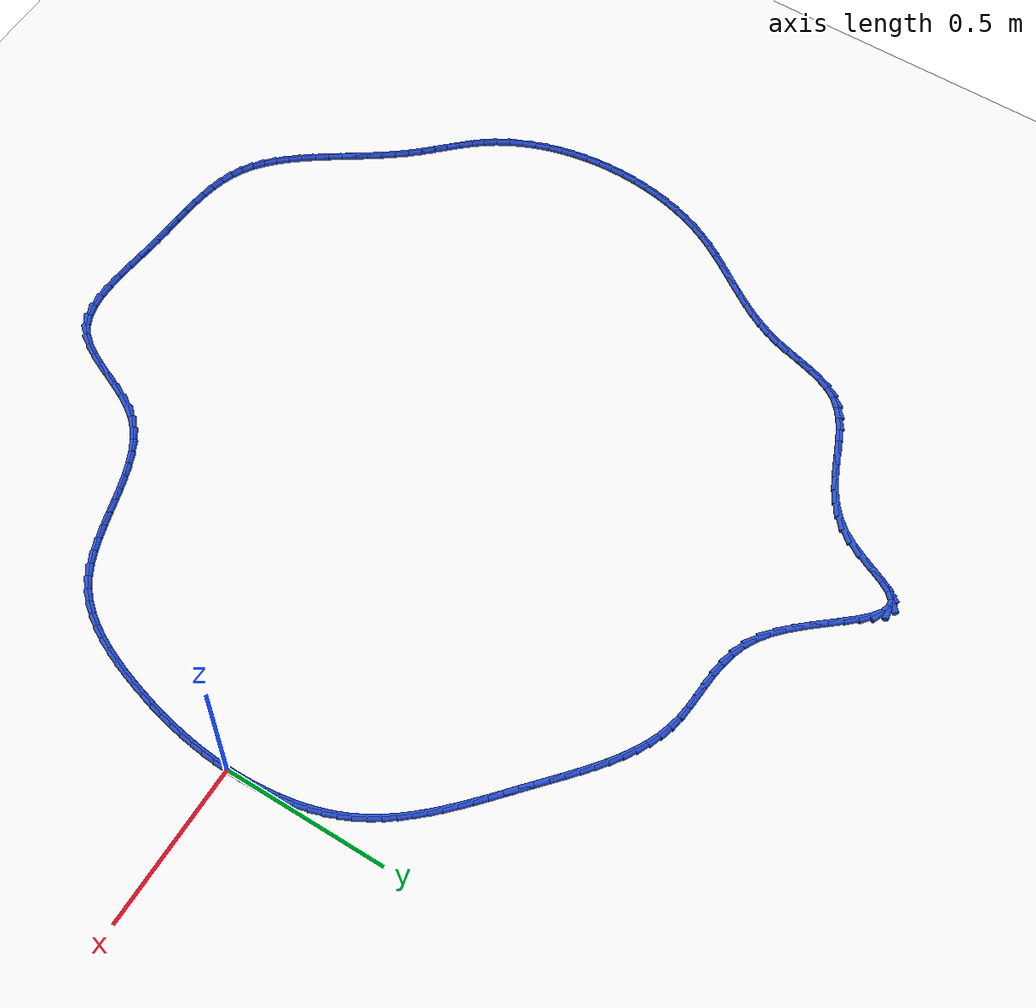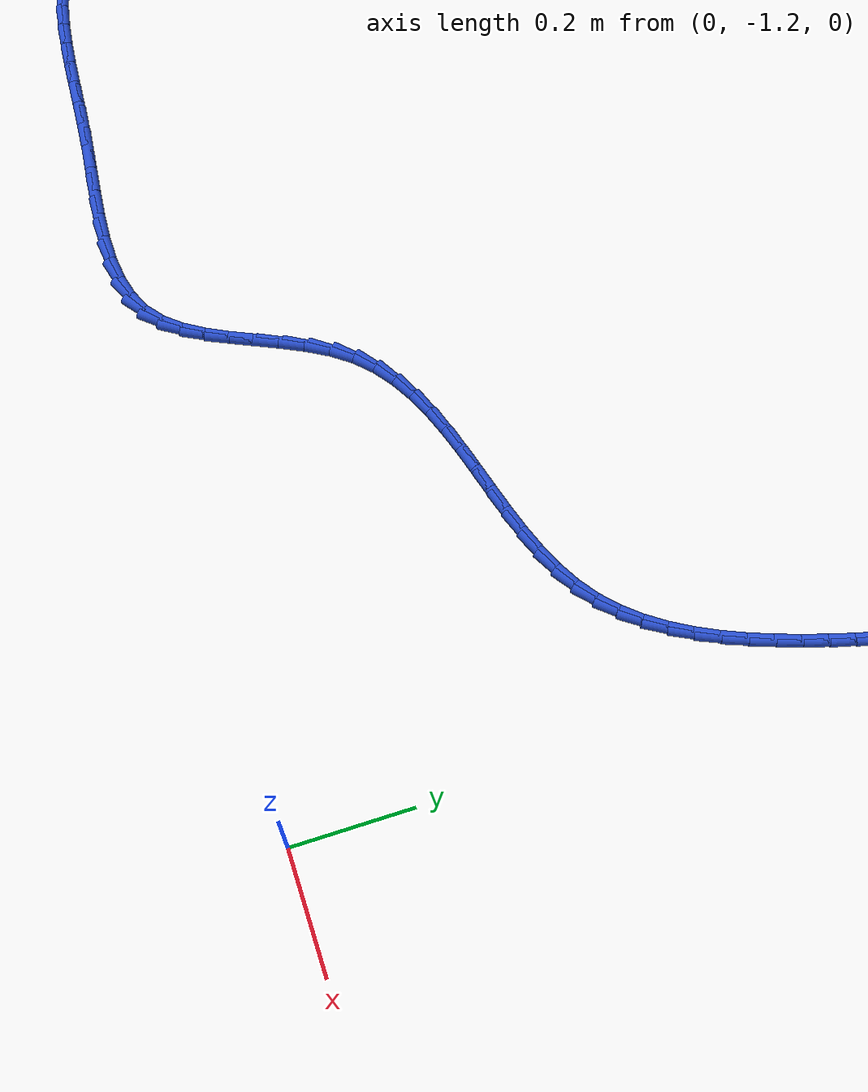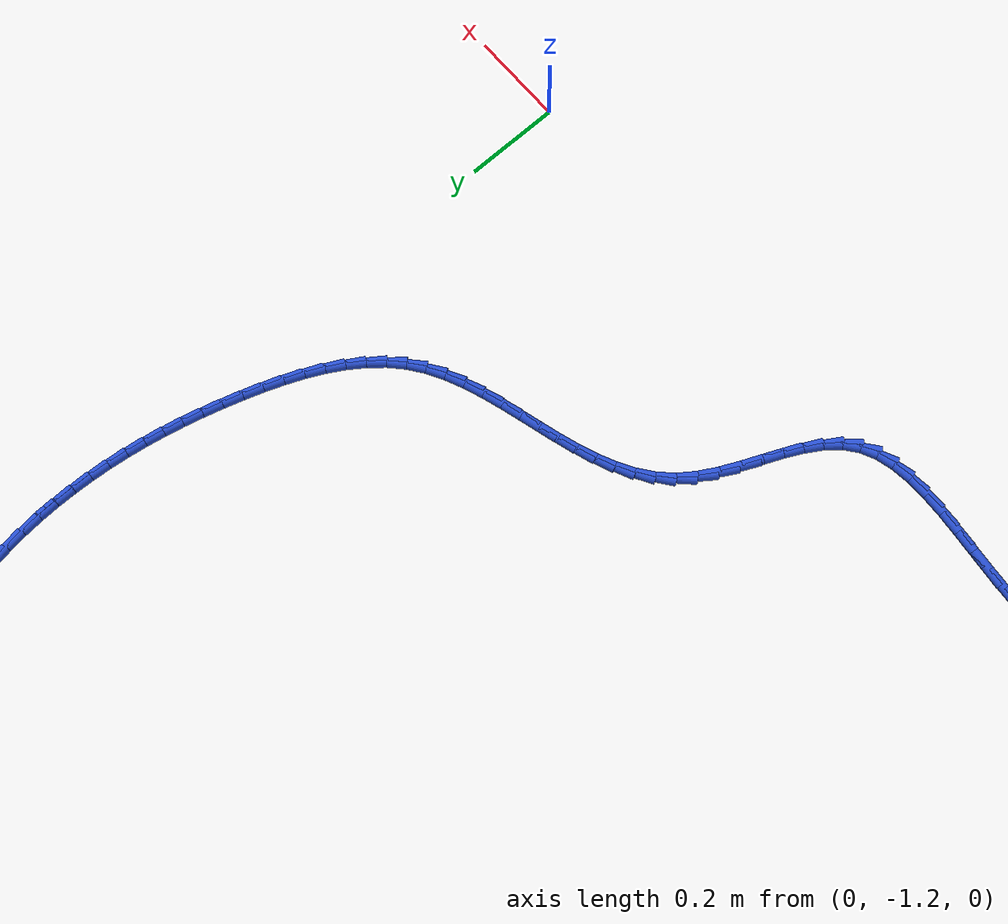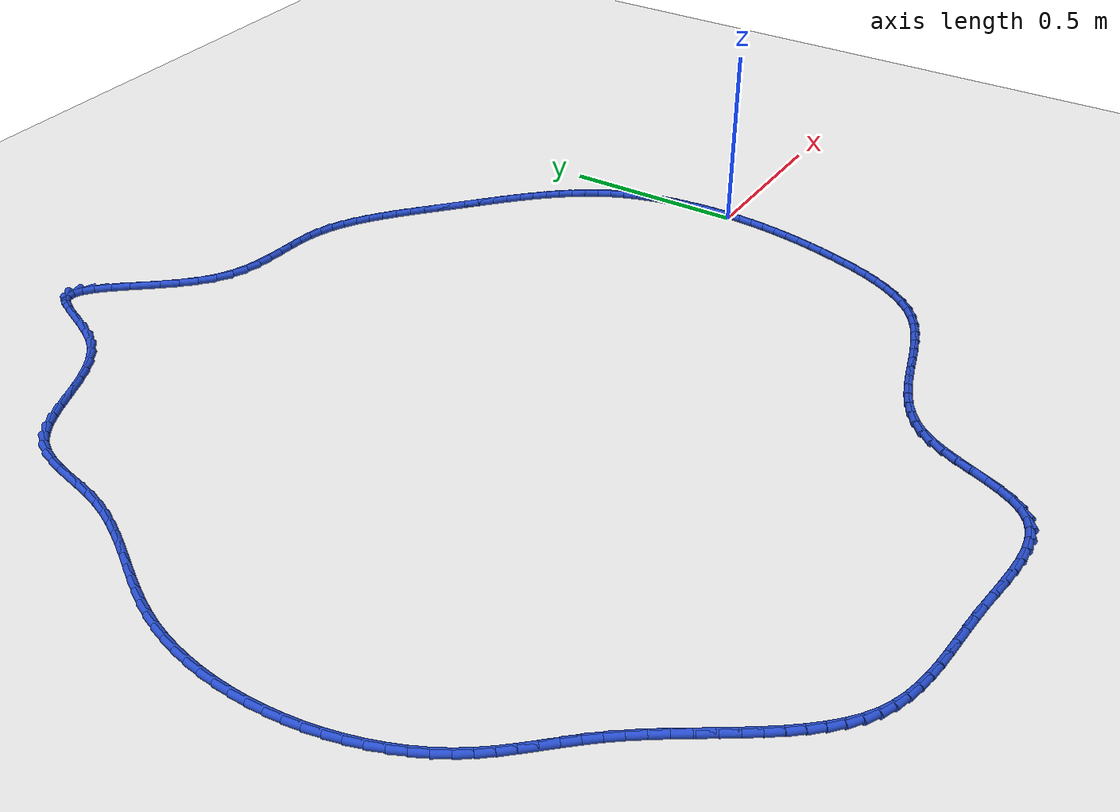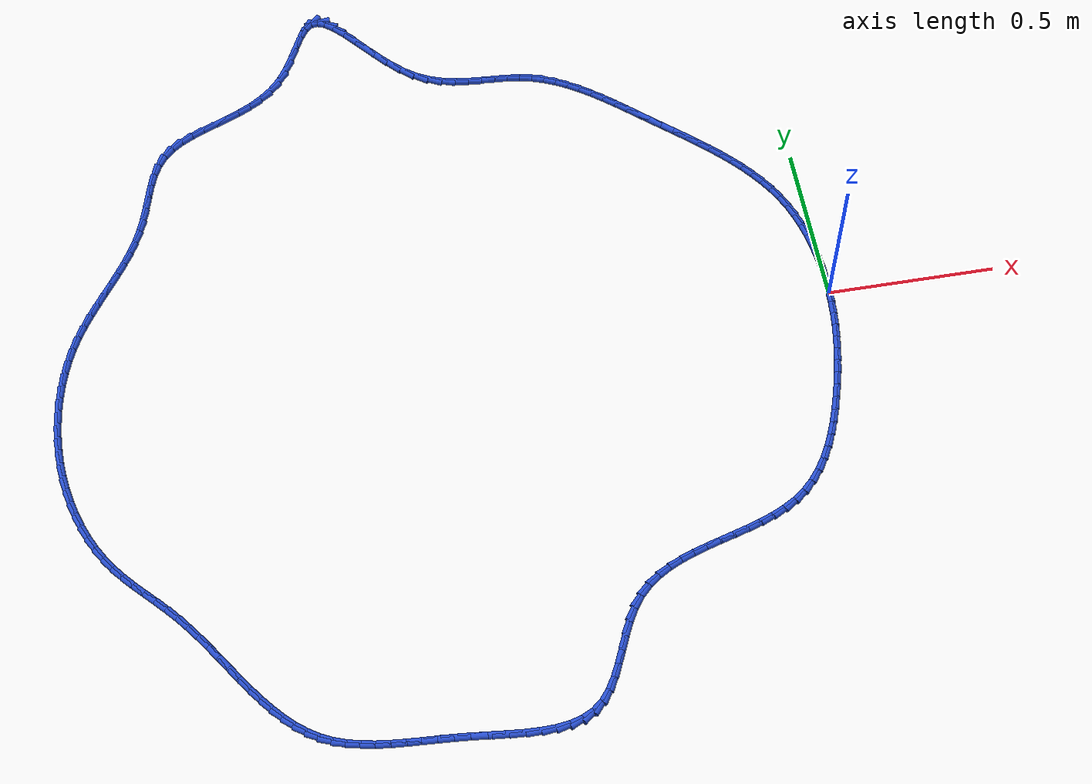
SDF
<sdf version="1.6">
 <world name="default">
  <light name="sun" type="directional">
   <pose>0 0 10 0 -0 0</pose>
   <diffuse>0.8 0.8 0.8 1</diffuse>
   <specular>0.2 0.2 0.2 1</specular>
   <attenuation>
    <range>1000</range>
    <constant>0.9</constant>
    <linear>0.01</linear>
    <quadratic>0.001</quadratic>
   </attenuation>
   <direction>-0.5 0.1 -0.9</direction>
  </light>
  <model name="ground_plane">
   <static>1</static>
   <link name="link">
    <collision name="collision">
     <geometry><plane><normal>0 0 1</normal><size>100 100</size></plane></geometry>
     <surface><friction><ode><mu>100</mu><mu2>50</mu2></ode></friction></surface>
    </collision>
    <visual name="visual">
     <cast_shadows>0</cast_shadows>
     <geometry><plane><normal>0 0 1</normal><size>100 100</size></plane></geometry>
     <material>
      <script><uri>file://media/materials/scripts/gazebo.material</uri><name>Gazebo/WhiteGlow</name></script>
     </material>
    </visual>
   </link>
  </model>
  <gravity>0 0 -9.8</gravity>
  <magnetic_field>6e-06 2.3e-05 -4.2e-05</magnetic_field>
  <atmosphere type="adiabatic"/>
  <physics name="default_physics" default="0" type="ode">
   <max_step_size>0.001</max_step_size>
   <real_time_factor>1</real_time_factor>
   <real_time_update_rate>1000</real_time_update_rate>
  </physics>
  <scene><ambient>0.4 0.4 0.4 1</ambient><background>0.7 0.7 0.7 1</background><shadows>1</shadows></scene>
  <spherical_coordinates>
   <surface_model>EARTH_WGS84</surface_model>
   <latitude_deg>0</latitude_deg>
   <longitude_deg>0</longitude_deg>
   <elevation>0</elevation>
   <heading_deg>0</heading_deg>
  </spherical_coordinates>
  <model name="line">
   <link name="link_0">
    <pose>-2.6020852139652106e-18 6.938893903907228e-18 0.01 0 1.57 1.5633253272327496</pose>
    <collision name="collision">
     <geometry><cylinder><radius>0.01</radius><length>0.08</length></cylinder></geometry>
    </collision>
    <visual name="visual">
     <material>
      <script><name>Gazebo/Blue</name><uri>file://media/materials/scripts/gazebo.material</uri></script>
     </material>
     <geometry><cylinder><radius>0.01</radius><length>0.08</length></cylinder></geometry>
    </visual>
   </link>
   <link name="link_1">
    <pose>0.0003042947766367383 0.04072937129704035 0.01 0 1.57 -1.5384906134617957</pose>
    <collision name="collision">
     <geometry><cylinder><radius>0.01</radius><length>0.08</length></cylinder></geometry>
    </collision>
    <visual name="visual">
     <material>
      <script><name>Gazebo/Blue</name><uri>file://media/materials/scripts/gazebo.material</uri></script>
     </material>
     <geometry><cylinder><radius>0.01</radius><length>0.08</length></cylinder></geometry>
    </visual>
   </link>
   <link name="link_2">
    <pose>-0.0010194835033201144 0.08169171470189848 0.01 0 1.57 -1.4957892981733807</pose>
    <collision name="collision">
     <geometry><cylinder><radius>0.01</radius><length>0.08</length></cylinder></geometry>
    </collision>
    <visual name="visual">
     <material>
      <script><name>Gazebo/Blue</name><uri>file://media/materials/scripts/gazebo.material</uri></script>
     </material>
     <geometry><cylinder><radius>0.01</radius><length>0.08</length></cylinder></geometry>
    </visual>
   </link>
   <link name="link_3">
    <pose>-0.004097125028575866 0.12264611266009999 0.01 0 1.57 -1.4496088059122907</pose>
    <collision name="collision">
     <geometry><cylinder><radius>0.01</radius><length>0.08</length></cylinder></geometry>
    </collision>
    <visual name="visual">
     <material>
      <script><name>Gazebo/Blue</name><uri>file://media/materials/scripts/gazebo.material</uri></script>
     </material>
     <geometry><cylinder><radius>0.01</radius><length>0.08</length></cylinder></geometry>
    </visual>
   </link>
   <link name="link_4">
    <pose>-0.009054419987835828 0.16335164761717058 0.01 0 1.57 -1.3993612007990788</pose>
    <collision name="collision">
     <geometry><cylinder><radius>0.01</radius><length>0.08</length></cylinder></geometry>
    </collision>
    <visual name="visual">
     <material>
      <script><name>Gazebo/Blue</name><uri>file://media/materials/scripts/gazebo.material</uri></script>
     </material>
     <geometry><cylinder><radius>0.01</radius><length>0.08</length></cylinder></geometry>
    </visual>
   </link>
   <link name="link_5">
    <pose>-0.016017158569805304 0.2035674020186357 0.01 0 1.57 -1.344429467422364</pose>
    <collision name="collision">
     <geometry><cylinder><radius>0.01</radius><length>0.08</length></cylinder></geometry>
    </collision>
    <visual name="visual">
     <material>
      <script><name>Gazebo/Blue</name><uri>file://media/materials/scripts/gazebo.material</uri></script>
     </material>
     <geometry><cylinder><radius>0.01</radius><length>0.08</length></cylinder></geometry>
    </visual>
   </link>
   <link name="link_6">
    <pose>-0.025111130963189586 0.243052458310021 0.01 0 1.57 -1.2841830512068837</pose>
    <collision name="collision">
     <geometry><cylinder><radius>0.01</radius><length>0.08</length></cylinder></geometry>
    </collision>
    <visual name="visual">
     <material>
      <script><name>Gazebo/Blue</name><uri>file://media/materials/scripts/gazebo.material</uri></script>
     </material>
     <geometry><cylinder><radius>0.01</radius><length>0.08</length></cylinder></geometry>
    </visual>
   </link>
   <link name="link_7">
    <pose>-0.036462127356694005 0.2815658989368522 0.01 0 1.57 -1.2180096415096069</pose>
    <collision name="collision">
     <geometry><cylinder><radius>0.01</radius><length>0.08</length></cylinder></geometry>
    </collision>
    <visual name="visual">
     <material>
      <script><name>Gazebo/Blue</name><uri>file://media/materials/scripts/gazebo.material</uri></script>
     </material>
     <geometry><cylinder><radius>0.01</radius><length>0.08</length></cylinder></geometry>
    </visual>
   </link>
   <link name="link_8">
    <pose>-0.05019593793902387 0.3188668063446548 0.01 0 1.57 -1.145462141478098</pose>
    <collision name="collision">
     <geometry><cylinder><radius>0.01</radius><length>0.08</length></cylinder></geometry>
    </collision>
    <visual name="visual">
     <material>
      <script><name>Gazebo/Blue</name><uri>file://media/materials/scripts/gazebo.material</uri></script>
     </material>
     <geometry><cylinder><radius>0.01</radius><length>0.08</length></cylinder></geometry>
    </visual>
   </link>
   <link name="link_9">
    <pose>-0.06643571476601769 0.3547173231201787 0.01 0 1.57 -1.0710275845918307</pose>
    <collision name="collision">
     <geometry><cylinder><radius>0.01</radius><length>0.08</length></cylinder></geometry>
    </collision>
    <visual name="visual">
     <material>
      <script><name>Gazebo/Blue</name><uri>file://media/materials/scripts/gazebo.material</uri></script>
     </material>
     <geometry><cylinder><radius>0.01</radius><length>0.08</length></cylinder></geometry>
    </visual>
   </link>
   <link name="link_10">
    <pose>-0.08517223144054736 0.38903314619394175 0.01 0 1.57 -1.00225199730104</pose>
    <collision name="collision">
     <geometry><cylinder><radius>0.01</radius><length>0.08</length></cylinder></geometry>
    </collision>
    <visual name="visual">
     <material>
      <script><name>Gazebo/Blue</name><uri>file://media/materials/scripts/gazebo.material</uri></script>
     </material>
     <geometry><cylinder><radius>0.01</radius><length>0.08</length></cylinder></geometry>
    </visual>
   </link>
   <link name="link_11">
    <pose>-0.1062047296215902 0.42195214280663146 0.01 0 1.57 -0.9404609084484915</pose>
    <collision name="collision">
     <geometry><cylinder><radius>0.01</radius><length>0.08</length></cylinder></geometry>
    </collision>
    <visual name="visual">
     <material>
      <script><name>Gazebo/Blue</name><uri>file://media/materials/scripts/gazebo.material</uri></script>
     </material>
     <geometry><cylinder><radius>0.01</radius><length>0.08</length></cylinder></geometry>
    </visual>
   </link>
   <link name="link_12">
    <pose>-0.12931747375452649 0.4536295532392889 0.01 0 1.57 -0.8860819304791444</pose>
    <collision name="collision">
     <geometry><cylinder><radius>0.01</radius><length>0.08</length></cylinder></geometry>
    </collision>
    <visual name="visual">
     <material>
      <script><name>Gazebo/Blue</name><uri>file://media/materials/scripts/gazebo.material</uri></script>
     </material>
     <geometry><cylinder><radius>0.01</radius><length>0.08</length></cylinder></geometry>
    </visual>
   </link>
   <link name="link_13">
    <pose>-0.15429472828473656 0.4842206177729553 0.01 0 1.57 -0.8392480904718871</pose>
    <collision name="collision">
     <geometry><cylinder><radius>0.01</radius><length>0.08</length></cylinder></geometry>
    </collision>
    <visual name="visual">
     <material>
      <script><name>Gazebo/Blue</name><uri>file://media/materials/scripts/gazebo.material</uri></script>
     </material>
     <geometry><cylinder><radius>0.01</radius><length>0.08</length></cylinder></geometry>
    </visual>
   </link>
   <link name="link_14">
    <pose>-0.18092075765760057 0.5138805766886716 0.01 0 1.57 -0.7998857184148789</pose>
    <collision name="collision">
     <geometry><cylinder><radius>0.01</radius><length>0.08</length></cylinder></geometry>
    </collision>
    <visual name="visual">
     <material>
      <script><name>Gazebo/Blue</name><uri>file://media/materials/scripts/gazebo.material</uri></script>
     </material>
     <geometry><cylinder><radius>0.01</radius><length>0.08</length></cylinder></geometry>
    </visual>
   </link>
   <link name="link_15">
    <pose>-0.20897982631849887 0.542764670267479 0.01 0 1.57 -0.7677964591328875</pose>
    <collision name="collision">
     <geometry><cylinder><radius>0.01</radius><length>0.08</length></cylinder></geometry>
    </collision>
    <visual name="visual">
     <material>
      <script><name>Gazebo/Blue</name><uri>file://media/materials/scripts/gazebo.material</uri></script>
     </material>
     <geometry><cylinder><radius>0.01</radius><length>0.08</length></cylinder></geometry>
    </visual>
   </link>
   <link name="link_16">
    <pose>-0.23825619871281184 0.5710281387904191 0.01 0 1.57 -0.7427239045836503</pose>
    <collision name="collision">
     <geometry><cylinder><radius>0.01</radius><length>0.08</length></cylinder></geometry>
    </collision>
    <visual name="visual">
     <material>
      <script><name>Gazebo/Blue</name><uri>file://media/materials/scripts/gazebo.material</uri></script>
     </material>
     <geometry><cylinder><radius>0.01</radius><length>0.08</length></cylinder></geometry>
    </visual>
   </link>
   <link name="link_17">
    <pose>-0.26853413928591957 0.5988262225385326 0.01 0 1.57 -0.7244025391302594</pose>
    <collision name="collision">
     <geometry><cylinder><radius>0.01</radius><length>0.08</length></cylinder></geometry>
    </collision>
    <visual name="visual">
     <material>
      <script><name>Gazebo/Blue</name><uri>file://media/materials/scripts/gazebo.material</uri></script>
     </material>
     <geometry><cylinder><radius>0.01</radius><length>0.08</length></cylinder></geometry>
    </visual>
   </link>
   <link name="link_18">
    <pose>-0.29959791248320244 0.6263141617928608 0.01 0 1.57 -0.7125906616806067</pose>
    <collision name="collision">
     <geometry><cylinder><radius>0.01</radius><length>0.08</length></cylinder></geometry>
    </collision>
    <visual name="visual">
     <material>
      <script><name>Gazebo/Blue</name><uri>file://media/materials/scripts/gazebo.material</uri></script>
     </material>
     <geometry><cylinder><radius>0.01</radius><length>0.08</length></cylinder></geometry>
    </visual>
   </link>
   <link name="link_19">
    <pose>-0.33123178275004067 0.6536471968344447 0.01 0 1.57 -0.7070903993795209</pose>
    <collision name="collision">
     <geometry><cylinder><radius>0.01</radius><length>0.08</length></cylinder></geometry>
    </collision>
    <visual name="visual">
     <material>
      <script><name>Gazebo/Blue</name><uri>file://media/materials/scripts/gazebo.material</uri></script>
     </material>
     <geometry><cylinder><radius>0.01</radius><length>0.08</length></cylinder></geometry>
    </visual>
   </link>
   <link name="link_20">
    <pose>-0.36322001453181474 0.680980567944326 0.01 0 1.57 -0.7077578900891363</pose>
    <collision name="collision">
     <geometry><cylinder><radius>0.01</radius><length>0.08</length></cylinder></geometry>
    </collision>
    <visual name="visual">
     <material>
      <script><name>Gazebo/Blue</name><uri>file://media/materials/scripts/gazebo.material</uri></script>
     </material>
     <geometry><cylinder><radius>0.01</radius><length>0.08</length></cylinder></geometry>
    </visual>
   </link>
   <link name="link_21">
    <pose>-0.3953468722739047 0.7084695154035453 0.01 0 1.57 -0.7127461964558518</pose>
    <collision name="collision">
     <geometry><cylinder><radius>0.01</radius><length>0.08</length></cylinder></geometry>
    </collision>
    <visual name="visual">
     <material>
      <script><name>Gazebo/Blue</name><uri>file://media/materials/scripts/gazebo.material</uri></script>
     </material>
     <geometry><cylinder><radius>0.01</radius><length>0.08</length></cylinder></geometry>
    </visual>
   </link>
   <link name="link_22">
    <pose>-0.42743500156394176 0.7362037679230788 0.01 0 1.57 -0.7119506680566565</pose>
    <collision name="collision">
     <geometry><cylinder><radius>0.01</radius><length>0.08</length></cylinder></geometry>
    </collision>
    <visual name="visual">
     <material>
      <script><name>Gazebo/Blue</name><uri>file://media/materials/scripts/gazebo.material</uri></script>
     </material>
     <geometry><cylinder><radius>0.01</radius><length>0.08</length></cylinder></geometry>
    </visual>
   </link>
   <link name="link_23">
    <pose>-0.45952732371604627 0.7638970724727846 0.01 0 1.57 -0.7017311433910982</pose>
    <collision name="collision">
     <geometry><cylinder><radius>0.01</radius><length>0.08</length></cylinder></geometry>
    </collision>
    <visual name="visual">
     <material>
      <script><name>Gazebo/Blue</name><uri>file://media/materials/scripts/gazebo.material</uri></script>
     </material>
     <geometry><cylinder><radius>0.01</radius><length>0.08</length></cylinder></geometry>
    </visual>
   </link>
   <link name="link_24">
    <pose>-0.4917451969610661 0.7911292945050753 0.01 0 1.57 -0.6818177769213483</pose>
    <collision name="collision">
     <geometry><cylinder><radius>0.01</radius><length>0.08</length></cylinder></geometry>
    </collision>
    <visual name="visual">
     <material>
      <script><name>Gazebo/Blue</name><uri>file://media/materials/scripts/gazebo.material</uri></script>
     </material>
     <geometry><cylinder><radius>0.01</radius><length>0.08</length></cylinder></geometry>
    </visual>
   </link>
   <link name="link_25">
    <pose>-0.5242100750947678 0.8174801363555947 0.01 0 1.57 -0.6517178875779612</pose>
    <collision name="collision">
     <geometry><cylinder><radius>0.01</radius><length>0.08</length></cylinder></geometry>
    </collision>
    <visual name="visual">
     <material>
      <script><name>Gazebo/Blue</name><uri>file://media/materials/scripts/gazebo.material</uri></script>
     </material>
     <geometry><cylinder><radius>0.01</radius><length>0.08</length></cylinder></geometry>
    </visual>
   </link>
   <link name="link_26">
    <pose>-0.5570434119129173 0.8425293003599874 0.01 0 1.57 -0.610744372104478</pose>
    <collision name="collision">
     <geometry><cylinder><radius>0.01</radius><length>0.08</length></cylinder></geometry>
    </collision>
    <visual name="visual">
     <material>
      <script><name>Gazebo/Blue</name><uri>file://media/materials/scripts/gazebo.material</uri></script>
     </material>
     <geometry><cylinder><radius>0.01</radius><length>0.08</length></cylinder></geometry>
    </visual>
   </link>
   <link name="link_27">
    <pose>-0.5903666612112809 0.8658564888538977 0.01 0 1.57 -0.5580859223085373</pose>
    <collision name="collision">
     <geometry><cylinder><radius>0.01</radius><length>0.08</length></cylinder></geometry>
    </collision>
    <visual name="visual">
     <material>
      <script><name>Gazebo/Blue</name><uri>file://media/materials/scripts/gazebo.material</uri></script>
     </material>
     <geometry><cylinder><radius>0.01</radius><length>0.08</length></cylinder></geometry>
    </visual>
   </link>
   <link name="link_28">
    <pose>-0.6243012767856253 0.8870414041729702 0.01 0 1.57 -0.4929404429563941</pose>
    <collision name="collision">
     <geometry><cylinder><radius>0.01</radius><length>0.08</length></cylinder></geometry>
    </collision>
    <visual name="visual">
     <material>
      <script><name>Gazebo/Blue</name><uri>file://media/materials/scripts/gazebo.material</uri></script>
     </material>
     <geometry><cylinder><radius>0.01</radius><length>0.08</length></cylinder></geometry>
    </visual>
   </link>
   <link name="link_29">
    <pose>-0.6589687124317164 0.905663748652849 0.01 0 1.57 -0.4147409092447706</pose>
    <collision name="collision">
     <geometry><cylinder><radius>0.01</radius><length>0.08</length></cylinder></geometry>
    </collision>
    <visual name="visual">
     <material>
      <script><name>Gazebo/Blue</name><uri>file://media/materials/scripts/gazebo.material</uri></script>
     </material>
     <geometry><cylinder><radius>0.01</radius><length>0.08</length></cylinder></geometry>
    </visual>
   </link>
   <link name="link_30">
    <pose>-0.6944904219453207 0.9213032246291789 0.01 0 1.57 -0.3234879603843398</pose>
    <collision name="collision">
     <geometry><cylinder><radius>0.01</radius><length>0.08</length></cylinder></geometry>
    </collision>
    <visual name="visual">
     <material>
      <script><name>Gazebo/Blue</name><uri>file://media/materials/scripts/gazebo.material</uri></script>
     </material>
     <geometry><cylinder><radius>0.01</radius><length>0.08</length></cylinder></geometry>
    </visual>
   </link>
   <link name="link_31">
    <pose>-0.7309878591222044 0.9335395344376037 0.01 0 1.57 -0.2210676943774228</pose>
    <collision name="collision">
     <geometry><cylinder><radius>0.01</radius><length>0.08</length></cylinder></geometry>
    </collision>
    <visual name="visual">
     <material>
      <script><name>Gazebo/Blue</name><uri>file://media/materials/scripts/gazebo.material</uri></script>
     </material>
     <geometry><cylinder><radius>0.01</radius><length>0.08</length></cylinder></geometry>
    </visual>
   </link>
   <link name="link_32">
    <pose>-0.7685750742174922 0.9419869142806971 0.01 0 1.57 -0.13162935804286813</pose>
    <collision name="collision">
     <geometry><cylinder><radius>0.01</radius><length>0.08</length></cylinder></geometry>
    </collision>
    <visual name="visual">
     <material>
      <script><name>Gazebo/Blue</name><uri>file://media/materials/scripts/gazebo.material</uri></script>
     </material>
     <geometry><cylinder><radius>0.01</radius><length>0.08</length></cylinder></geometry>
    </visual>
   </link>
   <link name="link_33">
    <pose>-0.8071861993922907 0.9470988295646305 0.01 0 1.57 -0.07842216635753575</pose>
    <collision name="collision">
     <geometry><cylinder><radius>0.01</radius><length>0.08</length></cylinder></geometry>
    </collision>
    <visual name="visual">
     <material>
      <script><name>Gazebo/Blue</name><uri>file://media/materials/scripts/gazebo.material</uri></script>
     </material>
     <geometry><cylinder><radius>0.01</radius><length>0.08</length></cylinder></geometry>
    </visual>
   </link>
   <link name="link_34">
    <pose>-0.8465699263620361 0.9501937339469584 0.01 0 1.57 -0.060983118279326766</pose>
    <collision name="collision">
     <geometry><cylinder><radius>0.01</radius><length>0.08</length></cylinder></geometry>
    </collision>
    <visual name="visual">
     <material>
      <script><name>Gazebo/Blue</name><uri>file://media/materials/scripts/gazebo.material</uri></script>
     </material>
     <geometry><cylinder><radius>0.01</radius><length>0.08</length></cylinder></geometry>
    </visual>
   </link>
   <link name="link_35">
    <pose>-0.8864664385147346 0.9526297682378362 0.01 0 1.57 -0.07793263973695852</pose>
    <collision name="collision">
     <geometry><cylinder><radius>0.01</radius><length>0.08</length></cylinder></geometry>
    </collision>
    <visual name="visual">
     <material>
      <script><name>Gazebo/Blue</name><uri>file://media/materials/scripts/gazebo.material</uri></script>
     </material>
     <geometry><cylinder><radius>0.01</radius><length>0.08</length></cylinder></geometry>
    </visual>
   </link>
   <link name="link_36">
    <pose>-0.9266159192383923 0.9557650732474188 0.01 0 1.57 -0.12864229530129664</pose>
    <collision name="collision">
     <geometry><cylinder><radius>0.01</radius><length>0.08</length></cylinder></geometry>
    </collision>
    <visual name="visual">
     <material>
      <script><name>Gazebo/Blue</name><uri>file://media/materials/scripts/gazebo.material</uri></script>
     </material>
     <geometry><cylinder><radius>0.01</radius><length>0.08</length></cylinder></geometry>
    </visual>
   </link>
   <link name="link_37">
    <pose>-0.966758551921015 0.9609577897858612 0.01 0 1.57 -0.21261341061862662</pose>
    <collision name="collision">
     <geometry><cylinder><radius>0.01</radius><length>0.08</length></cylinder></geometry>
    </collision>
    <visual name="visual">
     <material>
      <script><name>Gazebo/Blue</name><uri>file://media/materials/scripts/gazebo.material</uri></script>
     </material>
     <geometry><cylinder><radius>0.01</radius><length>0.08</length></cylinder></geometry>
    </visual>
   </link>
   <link name="link_38">
    <pose>-1.006634519950609 0.9695660586633188 0.01 0 1.57 -0.3278099549088953</pose>
    <collision name="collision">
     <geometry><cylinder><radius>0.01</radius><length>0.08</length></cylinder></geometry>
    </collision>
    <visual name="visual">
     <material>
      <script><name>Gazebo/Blue</name><uri>file://media/materials/scripts/gazebo.material</uri></script>
     </material>
     <geometry><cylinder><radius>0.01</radius><length>0.08</length></cylinder></geometry>
    </visual>
   </link>
   <link name="link_39">
    <pose>-1.0459840067151804 0.9829480206899466 0.01 0 1.57 -0.4684530588624157</pose>
    <collision name="collision">
     <geometry><cylinder><radius>0.01</radius><length>0.08</length></cylinder></geometry>
    </collision>
    <visual name="visual">
     <material>
      <script><name>Gazebo/Blue</name><uri>file://media/materials/scripts/gazebo.material</uri></script>
     </material>
     <geometry><cylinder><radius>0.01</radius><length>0.08</length></cylinder></geometry>
    </visual>
   </link>
   <link name="link_40">
    <pose>-1.0845471956027357 1.0024618166758996 0.01 0 1.57 -0.6207220399254244</pose>
    <collision name="collision">
     <geometry><cylinder><radius>0.01</radius><length>0.08</length></cylinder></geometry>
    </collision>
    <visual name="visual">
     <material>
      <script><name>Gazebo/Blue</name><uri>file://media/materials/scripts/gazebo.material</uri></script>
     </material>
     <geometry><cylinder><radius>0.01</radius><length>0.08</length></cylinder></geometry>
    </visual>
   </link>
   <link name="link_41">
    <pose>-1.122070296859322 1.0292908193727501 0.01 0 1.57 -0.7404278517348016</pose>
    <collision name="collision">
     <geometry><cylinder><radius>0.01</radius><length>0.08</length></cylinder></geometry>
    </collision>
    <visual name="visual">
     <material>
      <script><name>Gazebo/Blue</name><uri>file://media/materials/scripts/gazebo.material</uri></script>
     </material>
     <geometry><cylinder><radius>0.01</radius><length>0.08</length></cylinder></geometry>
    </visual>
   </link>
   <link name="link_42">
    <pose>-1.158373692164482 1.0624675631776197 0.01 0 1.57 -0.8153161581939347</pose>
    <collision name="collision">
     <geometry><cylinder><radius>0.01</radius><length>0.08</length></cylinder></geometry>
    </collision>
    <visual name="visual">
     <material>
      <script><name>Gazebo/Blue</name><uri>file://media/materials/scripts/gazebo.material</uri></script>
     </material>
     <geometry><cylinder><radius>0.01</radius><length>0.08</length></cylinder></geometry>
    </visual>
   </link>
   <link name="link_43">
    <pose>-1.1933276420944352 1.0995781840697993 0.01 0 1.57 -0.8564229438490615</pose>
    <collision name="collision">
     <geometry><cylinder><radius>0.01</radius><length>0.08</length></cylinder></geometry>
    </collision>
    <visual name="visual">
     <material>
      <script><name>Gazebo/Blue</name><uri>file://media/materials/scripts/gazebo.material</uri></script>
     </material>
     <geometry><cylinder><radius>0.01</radius><length>0.08</length></cylinder></geometry>
    </visual>
   </link>
   <link name="link_44">
    <pose>-1.2268033345110236 1.1381819284109935 0.01 0 1.57 -0.8684503086650068</pose>
    <collision name="collision">
     <geometry><cylinder><radius>0.01</radius><length>0.08</length></cylinder></geometry>
    </collision>
    <visual name="visual">
     <material>
      <script><name>Gazebo/Blue</name><uri>file://media/materials/scripts/gazebo.material</uri></script>
     </material>
     <geometry><cylinder><radius>0.01</radius><length>0.08</length></cylinder></geometry>
    </visual>
   </link>
   <link name="link_45">
    <pose>-1.2586719572760896 1.1758380425629074 0.01 0 1.57 -0.8495175865013076</pose>
    <collision name="collision">
     <geometry><cylinder><radius>0.01</radius><length>0.08</length></cylinder></geometry>
    </collision>
    <visual name="visual">
     <material>
      <script><name>Gazebo/Blue</name><uri>file://media/materials/scripts/gazebo.material</uri></script>
     </material>
     <geometry><cylinder><radius>0.01</radius><length>0.08</length></cylinder></geometry>
    </visual>
   </link>
   <link name="link_46">
    <pose>-1.2888046982514756 1.210105772887246 0.01 0 1.57 -0.7884056647588836</pose>
    <collision name="collision">
     <geometry><cylinder><radius>0.01</radius><length>0.08</length></cylinder></geometry>
    </collision>
    <visual name="visual">
     <material>
      <script><name>Gazebo/Blue</name><uri>file://media/materials/scripts/gazebo.material</uri></script>
     </material>
     <geometry><cylinder><radius>0.01</radius><length>0.08</length></cylinder></geometry>
    </visual>
   </link>
   <link name="link_47">
    <pose>-1.3170727452990234 1.2385443657457131 0.01 0 1.57 -0.6546790028297458</pose>
    <collision name="collision">
     <geometry><cylinder><radius>0.01</radius><length>0.08</length></cylinder></geometry>
    </collision>
    <visual name="visual">
     <material>
      <script><name>Gazebo/Blue</name><uri>file://media/materials/scripts/gazebo.material</uri></script>
     </material>
     <geometry><cylinder><radius>0.01</radius><length>0.08</length></cylinder></geometry>
    </visual>
   </link>
   <link name="link_48">
    <pose>-1.3433472862805753 1.2587130675000144 0.01 0 1.57 -0.3732457614078976</pose>
    <collision name="collision">
     <geometry><cylinder><radius>0.01</radius><length>0.08</length></cylinder></geometry>
    </collision>
    <visual name="visual">
     <material>
      <script><name>Gazebo/Blue</name><uri>file://media/materials/scripts/gazebo.material</uri></script>
     </material>
     <geometry><cylinder><radius>0.01</radius><length>0.08</length></cylinder></geometry>
    </visual>
   </link>
   <link name="link_49">
    <pose>-1.3674995090579736 1.268171124511854 0.01 0 1.57 0.1670605351684007</pose>
    <collision name="collision">
     <geometry><cylinder><radius>0.01</radius><length>0.08</length></cylinder></geometry>
    </collision>
    <visual name="visual">
     <material>
      <script><name>Gazebo/Blue</name><uri>file://media/materials/scripts/gazebo.material</uri></script>
     </material>
     <geometry><cylinder><radius>0.01</radius><length>0.08</length></cylinder></geometry>
    </visual>
   </link>
   <link name="link_50">
    <pose>-1.389400623779036 1.2644778900334017 0.01 0 1.57 0.7416526336656561</pose>
    <collision name="collision">
     <geometry><cylinder><radius>0.01</radius><length>0.08</length></cylinder></geometry>
    </collision>
    <visual name="visual">
     <material>
      <script><name>Gazebo/Blue</name><uri>file://media/materials/scripts/gazebo.material</uri></script>
     </material>
     <geometry><cylinder><radius>0.01</radius><length>0.08</length></cylinder></geometry>
    </visual>
   </link>
   <link name="link_51">
    <pose>-1.4091671485161363 1.2463692903857126 0.01 0 1.57 1.0112725498139092</pose>
    <collision name="collision">
     <geometry><cylinder><radius>0.01</radius><length>0.08</length></cylinder></geometry>
    </collision>
    <visual name="visual">
     <material>
      <script><name>Gazebo/Blue</name><uri>file://media/materials/scripts/gazebo.material</uri></script>
     </material>
     <geometry><cylinder><radius>0.01</radius><length>0.08</length></cylinder></geometry>
    </visual>
   </link>
   <link name="link_52">
    <pose>-1.4277679114213644 1.2166691960031093 0.01 0 1.57 1.1114456245779307</pose>
    <collision name="collision">
     <geometry><cylinder><radius>0.01</radius><length>0.08</length></cylinder></geometry>
    </collision>
    <visual name="visual">
     <material>
      <script><name>Gazebo/Blue</name><uri>file://media/materials/scripts/gazebo.material</uri></script>
     </material>
     <geometry><cylinder><radius>0.01</radius><length>0.08</length></cylinder></geometry>
    </visual>
   </link>
   <link name="link_53">
    <pose>-1.4463567268602624 1.1790887287091927 0.01 0 1.57 1.1293125882316797</pose>
    <collision name="collision">
     <geometry><cylinder><radius>0.01</radius><length>0.08</length></cylinder></geometry>
    </collision>
    <visual name="visual">
     <material>
      <script><name>Gazebo/Blue</name><uri>file://media/materials/scripts/gazebo.material</uri></script>
     </material>
     <geometry><cylinder><radius>0.01</radius><length>0.08</length></cylinder></geometry>
    </visual>
   </link>
   <link name="link_54">
    <pose>-1.4660874091983722 1.1373390103275618 0.01 0 1.57 1.0898182107142609</pose>
    <collision name="collision">
     <geometry><cylinder><radius>0.01</radius><length>0.08</length></cylinder></geometry>
    </collision>
    <visual name="visual">
     <material>
      <script><name>Gazebo/Blue</name><uri>file://media/materials/scripts/gazebo.material</uri></script>
     </material>
     <geometry><cylinder><radius>0.01</radius><length>0.08</length></cylinder></geometry>
    </visual>
   </link>
   <link name="link_55">
    <pose>-1.4881137728012364 1.0951311626818168 0.01 0 1.57 0.9916329180709903</pose>
    <collision name="collision">
     <geometry><cylinder><radius>0.01</radius><length>0.08</length></cylinder></geometry>
    </collision>
    <visual name="visual">
     <material>
      <script><name>Gazebo/Blue</name><uri>file://media/materials/scripts/gazebo.material</uri></script>
     </material>
     <geometry><cylinder><radius>0.01</radius><length>0.08</length></cylinder></geometry>
    </visual>
   </link>
   <link name="link_56">
    <pose>-1.5135894662443654 1.05617591910153 0.01 0 1.57 0.8385913575643416</pose>
    <collision name="collision">
     <geometry><cylinder><radius>0.01</radius><length>0.08</length></cylinder></geometry>
    </collision>
    <visual name="visual">
     <material>
      <script><name>Gazebo/Blue</name><uri>file://media/materials/scripts/gazebo.material</uri></script>
     </material>
     <geometry><cylinder><radius>0.01</radius><length>0.08</length></cylinder></geometry>
    </visual>
   </link>
   <link name="link_57">
    <pose>-1.5432427975626901 1.0231873169242487 0.01 0 1.57 0.6908493842331348</pose>
    <collision name="collision">
     <geometry><cylinder><radius>0.01</radius><length>0.08</length></cylinder></geometry>
    </collision>
    <visual name="visual">
     <material>
      <script><name>Gazebo/Blue</name><uri>file://media/materials/scripts/gazebo.material</uri></script>
     </material>
     <geometry><cylinder><radius>0.01</radius><length>0.08</length></cylinder></geometry>
    </visual>
   </link>
   <link name="link_58">
    <pose>-1.5764568360941484 0.9957271098707687 0.01 0 1.57 0.5697194353066316</pose>
    <collision name="collision">
     <geometry><cylinder><radius>0.01</radius><length>0.08</length></cylinder></geometry>
    </collision>
    <visual name="visual">
     <material>
      <script><name>Gazebo/Blue</name><uri>file://media/materials/scripts/gazebo.material</uri></script>
     </material>
     <geometry><cylinder><radius>0.01</radius><length>0.08</length></cylinder></geometry>
    </visual>
   </link>
   <link name="link_59">
    <pose>-1.6123493392254924 0.9727353489715665 0.01 0 1.57 0.4792086022467263</pose>
    <collision name="collision">
     <geometry><cylinder><radius>0.01</radius><length>0.08</length></cylinder></geometry>
    </collision>
    <visual name="visual">
     <material>
      <script><name>Gazebo/Blue</name><uri>file://media/materials/scripts/gazebo.material</uri></script>
     </material>
     <geometry><cylinder><radius>0.01</radius><length>0.08</length></cylinder></geometry>
    </visual>
   </link>
   <link name="link_60">
    <pose>-1.6500380643434776 0.9531520852571198 0.01 0 1.57 0.4199094469460347</pose>
    <collision name="collision">
     <geometry><cylinder><radius>0.01</radius><length>0.08</length></cylinder></geometry>
    </collision>
    <visual name="visual">
     <material>
      <script><name>Gazebo/Blue</name><uri>file://media/materials/scripts/gazebo.material</uri></script>
     </material>
     <geometry><cylinder><radius>0.01</radius><length>0.08</length></cylinder></geometry>
    </visual>
   </link>
   <link name="link_61">
    <pose>-1.6886407688348568 0.9359173697579058 0.01 0 1.57 0.3914436918524253</pose>
    <collision name="collision">
     <geometry><cylinder><radius>0.01</radius><length>0.08</length></cylinder></geometry>
    </collision>
    <visual name="visual">
     <material>
      <script><name>Gazebo/Blue</name><uri>file://media/materials/scripts/gazebo.material</uri></script>
     </material>
     <geometry><cylinder><radius>0.01</radius><length>0.08</length></cylinder></geometry>
    </visual>
   </link>
   <link name="link_62">
    <pose>-1.7272752100863842 0.9199712535044019 0.01 0 1.57 0.39420824676147287</pose>
    <collision name="collision">
     <geometry><cylinder><radius>0.01</radius><length>0.08</length></cylinder></geometry>
    </collision>
    <visual name="visual">
     <material>
      <script><name>Gazebo/Blue</name><uri>file://media/materials/scripts/gazebo.material</uri></script>
     </material>
     <geometry><cylinder><radius>0.01</radius><length>0.08</length></cylinder></geometry>
    </visual>
   </link>
   <link name="link_63">
    <pose>-1.7650591454848144 0.9042537875270851 0.01 0 1.57 0.43034216655012236</pose>
    <collision name="collision">
     <geometry><cylinder><radius>0.01</radius><length>0.08</length></cylinder></geometry>
    </collision>
    <visual name="visual">
     <material>
      <script><name>Gazebo/Blue</name><uri>file://media/materials/scripts/gazebo.material</uri></script>
     </material>
     <geometry><cylinder><radius>0.01</radius><length>0.08</length></cylinder></geometry>
    </visual>
   </link>
   <link name="link_64">
    <pose>-1.801110332416901 0.8877050228564329 0.01 0 1.57 0.503992973642419</pose>
    <collision name="collision">
     <geometry><cylinder><radius>0.01</radius><length>0.08</length></cylinder></geometry>
    </collision>
    <visual name="visual">
     <material>
      <script><name>Gazebo/Blue</name><uri>file://media/materials/scripts/gazebo.material</uri></script>
     </material>
     <geometry><cylinder><radius>0.01</radius><length>0.08</length></cylinder></geometry>
    </visual>
   </link>
   <link name="link_65">
    <pose>-1.834546528269398 0.8692650105229227 0.01 0 1.57 0.6203873943356049</pose>
    <collision name="collision">
     <geometry><cylinder><radius>0.01</radius><length>0.08</length></cylinder></geometry>
    </collision>
    <visual name="visual">
     <material>
      <script><name>Gazebo/Blue</name><uri>file://media/materials/scripts/gazebo.material</uri></script>
     </material>
     <geometry><cylinder><radius>0.01</radius><length>0.08</length></cylinder></geometry>
    </visual>
   </link>
   <link name="link_66">
    <pose>-1.86448549042906 0.8478738015570316 0.01 0 1.57 0.7823148605467306</pose>
    <collision name="collision">
     <geometry><cylinder><radius>0.01</radius><length>0.08</length></cylinder></geometry>
    </collision>
    <visual name="visual">
     <material>
      <script><name>Gazebo/Blue</name><uri>file://media/materials/scripts/gazebo.material</uri></script>
     </material>
     <geometry><cylinder><radius>0.01</radius><length>0.08</length></cylinder></geometry>
    </visual>
   </link>
   <link name="link_67">
    <pose>-1.8900449762826401 0.8224714469892371 0.01 0 1.57 0.9759069794002375</pose>
    <collision name="collision">
     <geometry><cylinder><radius>0.01</radius><length>0.08</length></cylinder></geometry>
    </collision>
    <visual name="visual">
     <material>
      <script><name>Gazebo/Blue</name><uri>file://media/materials/scripts/gazebo.material</uri></script>
     </material>
     <geometry><cylinder><radius>0.01</radius><length>0.08</length></cylinder></geometry>
    </visual>
   </link>
   <link name="link_68">
    <pose>-1.9105342181063238 0.792191491040128 0.01 0 1.57 1.1354763237626189</pose>
    <collision name="collision">
     <geometry><cylinder><radius>0.01</radius><length>0.08</length></cylinder></geometry>
    </collision>
    <visual name="visual">
     <material>
      <script><name>Gazebo/Blue</name><uri>file://media/materials/scripts/gazebo.material</uri></script>
     </material>
     <geometry><cylinder><radius>0.01</radius><length>0.08</length></cylinder></geometry>
    </visual>
   </link>
   <link name="link_69">
    <pose>-1.9266404734784466 0.7575600287371348 0.01 0 1.57 1.2396057637916114</pose>
    <collision name="collision">
     <geometry><cylinder><radius>0.01</radius><length>0.08</length></cylinder></geometry>
    </collision>
    <visual name="visual">
     <material>
      <script><name>Gazebo/Blue</name><uri>file://media/materials/scripts/gazebo.material</uri></script>
     </material>
     <geometry><cylinder><radius>0.01</radius><length>0.08</length></cylinder></geometry>
    </visual>
   </link>
   <link name="link_70">
    <pose>-1.939654412906323 0.7197129284984966 0.01 0 1.57 1.2969505598008424</pose>
    <collision name="collision">
     <geometry><cylinder><radius>0.01</radius><length>0.08</length></cylinder></geometry>
    </collision>
    <visual name="visual">
     <material>
      <script><name>Gazebo/Blue</name><uri>file://media/materials/scripts/gazebo.material</uri></script>
     </material>
     <geometry><cylinder><radius>0.01</radius><length>0.08</length></cylinder></geometry>
    </visual>
   </link>
   <link name="link_71">
    <pose>-1.9508692613529421 0.6797886401241595 0.01 0 1.57 1.3144901126773414</pose>
    <collision name="collision">
     <geometry><cylinder><radius>0.01</radius><length>0.08</length></cylinder></geometry>
    </collision>
    <visual name="visual">
     <material>
      <script><name>Gazebo/Blue</name><uri>file://media/materials/scripts/gazebo.material</uri></script>
     </material>
     <geometry><cylinder><radius>0.01</radius><length>0.08</length></cylinder></geometry>
    </visual>
   </link>
   <link name="link_72">
    <pose>-1.9615782437812923 0.6389256134140712 0.01 0 1.57 1.2952669515223125</pose>
    <collision name="collision">
     <geometry><cylinder><radius>0.01</radius><length>0.08</length></cylinder></geometry>
    </collision>
    <visual name="visual">
     <material>
      <script><name>Gazebo/Blue</name><uri>file://media/materials/scripts/gazebo.material</uri></script>
     </material>
     <geometry><cylinder><radius>0.01</radius><length>0.08</length></cylinder></geometry>
    </visual>
   </link>
   <link name="link_73">
    <pose>-1.9730745851543616 0.5982622981681783 0.01 0 1.57 1.2389703189672407</pose>
    <collision name="collision">
     <geometry><cylinder><radius>0.01</radius><length>0.08</length></cylinder></geometry>
    </collision>
    <visual name="visual">
     <material>
      <script><name>Gazebo/Blue</name><uri>file://media/materials/scripts/gazebo.material</uri></script>
     </material>
     <geometry><cylinder><radius>0.01</radius><length>0.08</length></cylinder></geometry>
    </visual>
   </link>
   <link name="link_74">
    <pose>-1.9866307097697866 0.558919735754001 0.01 0 1.57 1.1644974473168157</pose>
    <collision name="collision">
     <geometry><cylinder><radius>0.01</radius><length>0.08</length></cylinder></geometry>
    </collision>
    <visual name="visual">
     <material>
      <script><name>Gazebo/Blue</name><uri>file://media/materials/scripts/gazebo.material</uri></script>
     </material>
     <geometry><cylinder><radius>0.01</radius><length>0.08</length></cylinder></geometry>
    </visual>
   </link>
   <link name="link_75">
    <pose>-2.002774802437328 0.5213961007887207 0.01 0 1.57 1.0997018250241077</pose>
    <collision name="collision">
     <geometry><cylinder><radius>0.01</radius><length>0.08</length></cylinder></geometry>
    </collision>
    <visual name="visual">
     <material>
      <script><name>Gazebo/Blue</name><uri>file://media/materials/scripts/gazebo.material</uri></script>
     </material>
     <geometry><cylinder><radius>0.01</radius><length>0.08</length></cylinder></geometry>
    </visual>
   </link>
   <link name="link_76">
    <pose>-2.021103936546798 0.48541030482460273 0.01 0 1.57 1.0477742499370155</pose>
    <collision name="collision">
     <geometry><cylinder><radius>0.01</radius><length>0.08</length></cylinder></geometry>
    </collision>
    <visual name="visual">
     <material>
      <script><name>Gazebo/Blue</name><uri>file://media/materials/scripts/gazebo.material</uri></script>
     </material>
     <geometry><cylinder><radius>0.01</radius><length>0.08</length></cylinder></geometry>
    </visual>
   </link>
   <link name="link_77">
    <pose>-2.0411564215048665 0.4506320788318388 0.01 0 1.57 1.009527364947297</pose>
    <collision name="collision">
     <geometry><cylinder><radius>0.01</radius><length>0.08</length></cylinder></geometry>
    </collision>
    <visual name="visual">
     <material>
      <script><name>Gazebo/Blue</name><uri>file://media/materials/scripts/gazebo.material</uri></script>
     </material>
     <geometry><cylinder><radius>0.01</radius><length>0.08</length></cylinder></geometry>
    </visual>
   </link>
   <link name="link_78">
    <pose>-2.0624705667182024 0.4167311537806217 0.01 0 1.57 0.9853264081306271</pose>
    <collision name="collision">
     <geometry><cylinder><radius>0.01</radius><length>0.08</length></cylinder></geometry>
    </collision>
    <visual name="visual">
     <material>
      <script><name>Gazebo/Blue</name><uri>file://media/materials/scripts/gazebo.material</uri></script>
     </material>
     <geometry><cylinder><radius>0.01</radius><length>0.08</length></cylinder></geometry>
    </visual>
   </link>
   <link name="link_79">
    <pose>-2.0845846815934754 0.38337726064114247 0.01 0 1.57 0.9752900531677008</pose>
    <collision name="collision">
     <geometry><cylinder><radius>0.01</radius><length>0.08</length></cylinder></geometry>
    </collision>
    <visual name="visual">
     <material>
      <script><name>Gazebo/Blue</name><uri>file://media/materials/scripts/gazebo.material</uri></script>
     </material>
     <geometry><cylinder><radius>0.01</radius><length>0.08</length></cylinder></geometry>
    </visual>
   </link>
   <link name="link_80">
    <pose>-2.1070370755373578 0.35024013038359314 0.01 0 1.57 0.9794305694555699</pose>
    <collision name="collision">
     <geometry><cylinder><radius>0.01</radius><length>0.08</length></cylinder></geometry>
    </collision>
    <visual name="visual">
     <material>
      <script><name>Gazebo/Blue</name><uri>file://media/materials/scripts/gazebo.material</uri></script>
     </material>
     <geometry><cylinder><radius>0.01</radius><length>0.08</length></cylinder></geometry>
    </visual>
   </link>
   <link name="link_81">
    <pose>-2.1293660579565152 0.31698949397816606 0.01 0 1.57 0.9977138819164583</pose>
    <collision name="collision">
     <geometry><cylinder><radius>0.01</radius><length>0.08</length></cylinder></geometry>
    </collision>
    <visual name="visual">
     <material>
      <script><name>Gazebo/Blue</name><uri>file://media/materials/scripts/gazebo.material</uri></script>
     </material>
     <geometry><cylinder><radius>0.01</radius><length>0.08</length></cylinder></geometry>
    </visual>
   </link>
   <link name="link_82">
    <pose>-2.151109938257622 0.283295082395053 0.01 0 1.57 1.0300352773880856</pose>
    <collision name="collision">
     <geometry><cylinder><radius>0.01</radius><length>0.08</length></cylinder></geometry>
    </collision>
    <visual name="visual">
     <material>
      <script><name>Gazebo/Blue</name><uri>file://media/materials/scripts/gazebo.material</uri></script>
     </material>
     <geometry><cylinder><radius>0.01</radius><length>0.08</length></cylinder></geometry>
    </visual>
   </link>
   <link name="link_83">
    <pose>-2.171807025847345 0.24882662660444552 0.01 0 1.57 1.0761135076919783</pose>
    <collision name="collision">
     <geometry><cylinder><radius>0.01</radius><length>0.08</length></cylinder></geometry>
    </collision>
    <visual name="visual">
     <material>
      <script><name>Gazebo/Blue</name><uri>file://media/materials/scripts/gazebo.material</uri></script>
     </material>
     <geometry><cylinder><radius>0.01</radius><length>0.08</length></cylinder></geometry>
    </visual>
   </link>
   <link name="link_84">
    <pose>-2.190995630132355 0.21325385757653603 0.01 0 1.57 1.1347386535883401</pose>
    <collision name="collision">
     <geometry><cylinder><radius>0.01</radius><length>0.08</length></cylinder></geometry>
    </collision>
    <visual name="visual">
     <material>
      <script><name>Gazebo/Blue</name><uri>file://media/materials/scripts/gazebo.material</uri></script>
     </material>
     <geometry><cylinder><radius>0.01</radius><length>0.08</length></cylinder></geometry>
    </visual>
   </link>
   <link name="link_85">
    <pose>-2.20823093047843 0.1762661186521343 0.01 0 1.57 1.196757983180371</pose>
    <collision name="collision">
     <geometry><cylinder><radius>0.01</radius><length>0.08</length></cylinder></geometry>
    </collision>
    <visual name="visual">
     <material>
      <script><name>Gazebo/Blue</name><uri>file://media/materials/scripts/gazebo.material</uri></script>
     </material>
     <geometry><cylinder><radius>0.01</radius><length>0.08</length></cylinder></geometry>
    </visual>
   </link>
   <link name="link_86">
    <pose>-2.22331424143409 0.13783890054178347 0.01 0 1.57 1.2560015107695213</pose>
    <collision name="collision">
     <geometry><cylinder><radius>0.01</radius><length>0.08</length></cylinder></geometry>
    </collision>
    <visual name="visual">
     <material>
      <script><name>Gazebo/Blue</name><uri>file://media/materials/scripts/gazebo.material</uri></script>
     </material>
     <geometry><cylinder><radius>0.01</radius><length>0.08</length></cylinder></geometry>
    </visual>
   </link>
   <link name="link_87">
    <pose>-2.2362331868539087 0.09816429004476702 0.01 0 1.57 1.3127877106966452</pose>
    <collision name="collision">
     <geometry><cylinder><radius>0.01</radius><length>0.08</length></cylinder></geometry>
    </collision>
    <visual name="visual">
     <material>
      <script><name>Gazebo/Blue</name><uri>file://media/materials/scripts/gazebo.material</uri></script>
     </material>
     <geometry><cylinder><radius>0.01</radius><length>0.08</length></cylinder></geometry>
    </visual>
   </link>
   <link name="link_88">
    <pose>-2.2469800037567786 0.057439737049145026 0.01 0 1.57 1.3675908581591225</pose>
    <collision name="collision">
     <geometry><cylinder><radius>0.01</radius><length>0.08</length></cylinder></geometry>
    </collision>
    <visual name="visual">
     <material>
      <script><name>Gazebo/Blue</name><uri>file://media/materials/scripts/gazebo.material</uri></script>
     </material>
     <geometry><cylinder><radius>0.01</radius><length>0.08</length></cylinder></geometry>
    </visual>
   </link>
   <link name="link_89">
    <pose>-2.2555469291615933 0.015862691442978756 0.01 0 1.57 1.4208770040597383</pose>
    <collision name="collision">
     <geometry><cylinder><radius>0.01</radius><length>0.08</length></cylinder></geometry>
    </collision>
    <visual name="visual">
     <material>
      <script><name>Gazebo/Blue</name><uri>file://media/materials/scripts/gazebo.material</uri></script>
     </material>
     <geometry><cylinder><radius>0.01</radius><length>0.08</length></cylinder></geometry>
    </visual>
   </link>
   <link name="link_90">
    <pose>-2.2619262000872453 -0.02636939688567163 0.01 0 1.57 1.4731021200910597</pose>
    <collision name="collision">
     <geometry><cylinder><radius>0.01</radius><length>0.08</length></cylinder></geometry>
    </collision>
    <visual name="visual">
     <material>
      <script><name>Gazebo/Blue</name><uri>file://media/materials/scripts/gazebo.material</uri></script>
     </material>
     <geometry><cylinder><radius>0.01</radius><length>0.08</length></cylinder></geometry>
    </visual>
   </link>
   <link name="link_91">
    <pose>-2.2661100535526284 -0.06905907804874584 0.01 0 1.57 1.5247130012874424</pose>
    <collision name="collision">
     <geometry><cylinder><radius>0.01</radius><length>0.08</length></cylinder></geometry>
    </collision>
    <visual name="visual">
     <material>
      <script><name>Gazebo/Blue</name><uri>file://media/materials/scripts/gazebo.material</uri></script>
     </material>
     <geometry><cylinder><radius>0.01</radius><length>0.08</length></cylinder></geometry>
    </visual>
   </link>
   <link name="link_92">
    <pose>-2.2680907265766335 -0.11200890215818404 0.01 0 1.57 -1.5654428108005716</pose>
    <collision name="collision">
     <geometry><cylinder><radius>0.01</radius><length>0.08</length></cylinder></geometry>
    </collision>
    <visual name="visual">
     <material>
      <script><name>Gazebo/Blue</name><uri>file://media/materials/scripts/gazebo.material</uri></script>
     </material>
     <geometry><cylinder><radius>0.01</radius><length>0.08</length></cylinder></geometry>
    </visual>
   </link>
   <link name="link_93">
    <pose>-2.2678604561781555 -0.15502141932592417 0.01 0 1.57 -1.513742996611289</pose>
    <collision name="collision">
     <geometry><cylinder><radius>0.01</radius><length>0.08</length></cylinder></geometry>
    </collision>
    <visual name="visual">
     <material>
      <script><name>Gazebo/Blue</name><uri>file://media/materials/scripts/gazebo.material</uri></script>
     </material>
     <geometry><cylinder><radius>0.01</radius><length>0.08</length></cylinder></geometry>
    </visual>
   </link>
   <link name="link_94">
    <pose>-2.2654114793760867 -0.19789917966390663 0.01 0 1.57 -1.461342808545094</pose>
    <collision name="collision">
     <geometry><cylinder><radius>0.01</radius><length>0.08</length></cylinder></geometry>
    </collision>
    <visual name="visual">
     <material>
      <script><name>Gazebo/Blue</name><uri>file://media/materials/scripts/gazebo.material</uri></script>
     </material>
     <geometry><cylinder><radius>0.01</radius><length>0.08</length></cylinder></geometry>
    </visual>
   </link>
   <link name="link_95">
    <pose>-2.2607360331893203 -0.24044473328407087 0.01 0 1.57 -1.4078013711453197</pose>
    <collision name="collision">
     <geometry><cylinder><radius>0.01</radius><length>0.08</length></cylinder></geometry>
    </collision>
    <visual name="visual">
     <material>
      <script><name>Gazebo/Blue</name><uri>file://media/materials/scripts/gazebo.material</uri></script>
     </material>
     <geometry><cylinder><radius>0.01</radius><length>0.08</length></cylinder></geometry>
    </visual>
   </link>
   <link name="link_96">
    <pose>-2.2538263546367476 -0.2824606302983564 0.01 0 1.57 -1.3526724298620056</pose>
    <collision name="collision">
     <geometry><cylinder><radius>0.01</radius><length>0.08</length></cylinder></geometry>
    </collision>
    <visual name="visual">
     <material>
      <script><name>Gazebo/Blue</name><uri>file://media/materials/scripts/gazebo.material</uri></script>
     </material>
     <geometry><cylinder><radius>0.01</radius><length>0.08</length></cylinder></geometry>
    </visual>
   </link>
   <link name="link_97">
    <pose>-2.2446746807372633 -0.3237494208187028 0.01 0 1.57 -1.2955044699338374</pose>
    <collision name="collision">
     <geometry><cylinder><radius>0.01</radius><length>0.08</length></cylinder></geometry>
    </collision>
    <visual name="visual">
     <material>
      <script><name>Gazebo/Blue</name><uri>file://media/materials/scripts/gazebo.material</uri></script>
     </material>
     <geometry><cylinder><radius>0.01</radius><length>0.08</length></cylinder></geometry>
    </visual>
   </link>
   <link name="link_98">
    <pose>-2.2332732485097595 -0.3641136549570504 0.01 0 1.57 -1.235843933882016</pose>
    <collision name="collision">
     <geometry><cylinder><radius>0.01</radius><length>0.08</length></cylinder></geometry>
    </collision>
    <visual name="visual">
     <material>
      <script><name>Gazebo/Blue</name><uri>file://media/materials/scripts/gazebo.material</uri></script>
     </material>
     <geometry><cylinder><radius>0.01</radius><length>0.08</length></cylinder></geometry>
    </visual>
   </link>
   <link name="link_99">
    <pose>-2.21961429497313 -0.4033558828253371 0.01 0 1.57 -1.1732428974885665</pose>
    <collision name="collision">
     <geometry><cylinder><radius>0.01</radius><length>0.08</length></cylinder></geometry>
    </collision>
    <visual name="visual">
     <material>
      <script><name>Gazebo/Blue</name><uri>file://media/materials/scripts/gazebo.material</uri></script>
     </material>
     <geometry><cylinder><radius>0.01</radius><length>0.08</length></cylinder></geometry>
    </visual>
   </link>
   <link name="link_100">
    <pose>-2.2036900571462663 -0.4412786545355032 0.01 0 1.57 -1.107272831513398</pose>
    <collision name="collision">
     <geometry><cylinder><radius>0.01</radius><length>0.08</length></cylinder></geometry>
    </collision>
    <visual name="visual">
     <material>
      <script><name>Gazebo/Blue</name><uri>file://media/materials/scripts/gazebo.material</uri></script>
     </material>
     <geometry><cylinder><radius>0.01</radius><length>0.08</length></cylinder></geometry>
    </visual>
   </link>
   <link name="link_101">
    <pose>-2.1854927720480624 -0.47768452019948826 0.01 0 1.57 -1.0375461842193756</pose>
    <collision name="collision">
     <geometry><cylinder><radius>0.01</radius><length>0.08</length></cylinder></geometry>
    </collision>
    <visual name="visual">
     <material>
      <script><name>Gazebo/Blue</name><uri>file://media/materials/scripts/gazebo.material</uri></script>
     </material>
     <geometry><cylinder><radius>0.01</radius><length>0.08</length></cylinder></geometry>
    </visual>
   </link>
   <link name="link_102">
    <pose>-2.165014676697411 -0.5123760299292319 0.01 0 1.57 -0.9638163096061111</pose>
    <collision name="collision">
     <geometry><cylinder><radius>0.01</radius><length>0.08</length></cylinder></geometry>
    </collision>
    <visual name="visual">
     <material>
      <script><name>Gazebo/Blue</name><uri>file://media/materials/scripts/gazebo.material</uri></script>
     </material>
     <geometry><cylinder><radius>0.01</radius><length>0.08</length></cylinder></geometry>
    </visual>
   </link>
   <link name="link_103">
    <pose>-2.142249682725304 -0.5451581563092984 0.01 0 1.57 -0.8935777648873438</pose>
    <collision name="collision">
     <geometry><cylinder><radius>0.01</radius><length>0.08</length></cylinder></geometry>
    </collision>
    <visual name="visual">
     <material>
      <script><name>Gazebo/Blue</name><uri>file://media/materials/scripts/gazebo.material</uri></script>
     </material>
     <geometry><cylinder><radius>0.01</radius><length>0.08</length></cylinder></geometry>
    </visual>
   </link>
   <link name="link_104">
    <pose>-2.1173724133612946 -0.5760972870307615 0.01 0 1.57 -0.841972257227343</pose>
    <collision name="collision">
     <geometry><cylinder><radius>0.01</radius><length>0.08</length></cylinder></geometry>
    </collision>
    <visual name="visual">
     <material>
      <script><name>Gazebo/Blue</name><uri>file://media/materials/scripts/gazebo.material</uri></script>
     </material>
     <geometry><cylinder><radius>0.01</radius><length>0.08</length></cylinder></geometry>
    </visual>
   </link>
   <link name="link_105">
    <pose>-2.0908972500763414 -0.6057512997475669 0.01 0 1.57 -0.8112300291535598</pose>
    <collision name="collision">
     <geometry><cylinder><radius>0.01</radius><length>0.08</length></cylinder></geometry>
    </collision>
    <visual name="visual">
     <material>
      <script><name>Gazebo/Blue</name><uri>file://media/materials/scripts/gazebo.material</uri></script>
     </material>
     <geometry><cylinder><radius>0.01</radius><length>0.08</length></cylinder></geometry>
    </visual>
   </link>
   <link name="link_106">
    <pose>-2.063376090027967 -0.6347323418300238 0.01 0 1.57 -0.8012912935177922</pose>
    <collision name="collision">
     <geometry><cylinder><radius>0.01</radius><length>0.08</length></cylinder></geometry>
    </collision>
    <visual name="visual">
     <material>
      <script><name>Gazebo/Blue</name><uri>file://media/materials/scripts/gazebo.material</uri></script>
     </material>
     <geometry><cylinder><radius>0.01</radius><length>0.08</length></cylinder></geometry>
    </visual>
   </link>
   <link name="link_107">
    <pose>-2.035360830373688 -0.66365256064844 0.01 0 1.57 -0.8117564498503885</pose>
    <collision name="collision">
     <geometry><cylinder><radius>0.01</radius><length>0.08</length></cylinder></geometry>
    </collision>
    <visual name="visual">
     <material>
      <script><name>Gazebo/Blue</name><uri>file://media/materials/scripts/gazebo.material</uri></script>
     </material>
     <geometry><cylinder><radius>0.01</radius><length>0.08</length></cylinder></geometry>
    </visual>
   </link>
   <link name="link_108">
    <pose>-2.0074033682710235 -0.6931241035731239 0.01 0 1.57 -0.8420310426290951</pose>
    <collision name="collision">
     <geometry><cylinder><radius>0.01</radius><length>0.08</length></cylinder></geometry>
    </collision>
    <visual name="visual">
     <material>
      <script><name>Gazebo/Blue</name><uri>file://media/materials/scripts/gazebo.material</uri></script>
     </material>
     <geometry><cylinder><radius>0.01</radius><length>0.08</length></cylinder></geometry>
    </visual>
   </link>
   <link name="link_109">
    <pose>-1.9800556008774914 -0.7237591179743844 0.01 0 1.57 -0.8867970858583996</pose>
    <collision name="collision">
     <geometry><cylinder><radius>0.01</radius><length>0.08</length></cylinder></geometry>
    </collision>
    <visual name="visual">
     <material>
      <script><name>Gazebo/Blue</name><uri>file://media/materials/scripts/gazebo.material</uri></script>
     </material>
     <geometry><cylinder><radius>0.01</radius><length>0.08</length></cylinder></geometry>
    </visual>
   </link>
   <link name="link_110">
    <pose>-1.9537548841078605 -0.7560181665348114 0.01 0 1.57 -0.925205953682807</pose>
    <collision name="collision">
     <geometry><cylinder><radius>0.01</radius><length>0.08</length></cylinder></geometry>
    </collision>
    <visual name="visual">
     <material>
      <script><name>Gazebo/Blue</name><uri>file://media/materials/scripts/gazebo.material</uri></script>
     </material>
     <geometry><cylinder><radius>0.01</radius><length>0.08</length></cylinder></geometry>
    </visual>
   </link>
   <link name="link_111">
    <pose>-1.9284108943409997 -0.7896634771211576 0.01 0 1.57 -0.9520745155772437</pose>
    <collision name="collision">
     <geometry><cylinder><radius>0.01</radius><length>0.08</length></cylinder></geometry>
    </collision>
    <visual name="visual">
     <material>
      <script><name>Gazebo/Blue</name><uri>file://media/materials/scripts/gazebo.material</uri></script>
     </material>
     <geometry><cylinder><radius>0.01</radius><length>0.08</length></cylinder></geometry>
    </visual>
   </link>
   <link name="link_112">
    <pose>-1.9037814509502091 -0.8242563089690158 0.01 0 1.57 -0.9680304342753239</pose>
    <collision name="collision">
     <geometry><cylinder><radius>0.01</radius><length>0.08</length></cylinder></geometry>
    </collision>
    <visual name="visual">
     <material>
      <script><name>Gazebo/Blue</name><uri>file://media/materials/scripts/gazebo.material</uri></script>
     </material>
     <geometry><cylinder><radius>0.01</radius><length>0.08</length></cylinder></geometry>
    </visual>
   </link>
   <link name="link_113">
    <pose>-1.8796243595447646 -0.8593579030985751 0.01 0 1.57 -0.9734204623193966</pose>
    <collision name="collision">
     <geometry><cylinder><radius>0.01</radius><length>0.08</length></cylinder></geometry>
    </collision>
    <visual name="visual">
     <material>
      <script><name>Gazebo/Blue</name><uri>file://media/materials/scripts/gazebo.material</uri></script>
     </material>
     <geometry><cylinder><radius>0.01</radius><length>0.08</length></cylinder></geometry>
    </visual>
   </link>
   <link name="link_114">
    <pose>-1.8556974257339445 -0.8945295005300241 0.01 0 1.57 -0.9682745543254329</pose>
    <collision name="collision">
     <geometry><cylinder><radius>0.01</radius><length>0.08</length></cylinder></geometry>
    </collision>
    <visual name="visual">
     <material>
      <script><name>Gazebo/Blue</name><uri>file://media/materials/scripts/gazebo.material</uri></script>
     </material>
     <geometry><cylinder><radius>0.01</radius><length>0.08</length></cylinder></geometry>
    </visual>
   </link>
   <link name="link_115">
    <pose>-1.8317584551270234 -0.9293323422835527 0.01 0 1.57 -0.9522859446952432</pose>
    <collision name="collision">
     <geometry><cylinder><radius>0.01</radius><length>0.08</length></cylinder></geometry>
    </collision>
    <visual name="visual">
     <material>
      <script><name>Gazebo/Blue</name><uri>file://media/materials/scripts/gazebo.material</uri></script>
     </material>
     <geometry><cylinder><radius>0.01</radius><length>0.08</length></cylinder></geometry>
    </visual>
   </link>
   <link name="link_116">
    <pose>-1.8075652533332809 -0.963327669379348 0.01 0 1.57 -0.9248016290844787</pose>
    <collision name="collision">
     <geometry><cylinder><radius>0.01</radius><length>0.08</length></cylinder></geometry>
    </collision>
    <visual name="visual">
     <material>
      <script><name>Gazebo/Blue</name><uri>file://media/materials/scripts/gazebo.material</uri></script>
     </material>
     <geometry><cylinder><radius>0.01</radius><length>0.08</length></cylinder></geometry>
    </visual>
   </link>
   <link name="link_117">
    <pose>-1.7828756259619927 -0.9960767228375995 0.01 0 1.57 -0.8848310238092505</pose>
    <collision name="collision">
     <geometry><cylinder><radius>0.01</radius><length>0.08</length></cylinder></geometry>
    </collision>
    <visual name="visual">
     <material>
      <script><name>Gazebo/Blue</name><uri>file://media/materials/scripts/gazebo.material</uri></script>
     </material>
     <geometry><cylinder><radius>0.01</radius><length>0.08</length></cylinder></geometry>
    </visual>
   </link>
   <link name="link_118">
    <pose>-1.757447378622435 -1.027140743678496 0.01 0 1.57 -0.8310971277487728</pose>
    <collision name="collision">
     <geometry><cylinder><radius>0.01</radius><length>0.08</length></cylinder></geometry>
    </collision>
    <visual name="visual">
     <material>
      <script><name>Gazebo/Blue</name><uri>file://media/materials/scripts/gazebo.material</uri></script>
     </material>
     <geometry><cylinder><radius>0.01</radius><length>0.08</length></cylinder></geometry>
    </visual>
   </link>
   <link name="link_119">
    <pose>-1.7310383169238863 -1.0560809729222274 0.01 0 1.57 -0.7621770536977609</pose>
    <collision name="collision">
     <geometry><cylinder><radius>0.01</radius><length>0.08</length></cylinder></geometry>
    </collision>
    <visual name="visual">
     <material>
      <script><name>Gazebo/Blue</name><uri>file://media/materials/scripts/gazebo.material</uri></script>
     </material>
     <geometry><cylinder><radius>0.01</radius><length>0.08</length></cylinder></geometry>
    </visual>
   </link>
   <link name="link_120">
    <pose>-1.703406246475622 -1.0824586515889818 0.01 0 1.57 -0.6768027301396479</pose>
    <collision name="collision">
     <geometry><cylinder><radius>0.01</radius><length>0.08</length></cylinder></geometry>
    </collision>
    <visual name="visual">
     <material>
      <script><name>Gazebo/Blue</name><uri>file://media/materials/scripts/gazebo.material</uri></script>
     </material>
     <geometry><cylinder><radius>0.01</radius><length>0.08</length></cylinder></geometry>
    </visual>
   </link>
   <link name="link_121">
    <pose>-1.6743089728869198 -1.1058350206989473 0.01 0 1.57 -0.5743932949277449</pose>
    <collision name="collision">
     <geometry><cylinder><radius>0.01</radius><length>0.08</length></cylinder></geometry>
    </collision>
    <visual name="visual">
     <material>
      <script><name>Gazebo/Blue</name><uri>file://media/materials/scripts/gazebo.material</uri></script>
     </material>
     <geometry><cylinder><radius>0.01</radius><length>0.08</length></cylinder></geometry>
    </visual>
   </link>
   <link name="link_122">
    <pose>-1.643504301767057 -1.125771321272314 0.01 0 1.57 -0.45762023915636185</pose>
    <collision name="collision">
     <geometry><cylinder><radius>0.01</radius><length>0.08</length></cylinder></geometry>
    </collision>
    <visual name="visual">
     <material>
      <script><name>Gazebo/Blue</name><uri>file://media/materials/scripts/gazebo.material</uri></script>
     </material>
     <geometry><cylinder><radius>0.01</radius><length>0.08</length></cylinder></geometry>
    </visual>
   </link>
   <link name="link_123">
    <pose>-1.6107739519585216 -1.141890636737874 0.01 0 1.57 -0.3468805183744202</pose>
    <collision name="collision">
     <geometry><cylinder><radius>0.01</radius><length>0.08</length></cylinder></geometry>
    </collision>
    <visual name="visual">
     <material>
      <script><name>Gazebo/Blue</name><uri>file://media/materials/scripts/gazebo.material</uri></script>
     </material>
     <geometry><cylinder><radius>0.01</radius><length>0.08</length></cylinder></geometry>
    </visual>
   </link>
   <link name="link_124">
    <pose>-1.5761308656827624 -1.1544140211356653 0.01 0 1.57 -0.2547856281966714</pose>
    <collision name="collision">
     <geometry><cylinder><radius>0.01</radius><length>0.08</length></cylinder></geometry>
    </collision>
    <visual name="visual">
     <material>
      <script><name>Gazebo/Blue</name><uri>file://media/materials/scripts/gazebo.material</uri></script>
     </material>
     <geometry><cylinder><radius>0.01</radius><length>0.08</length></cylinder></geometry>
    </visual>
   </link>
   <link name="link_125">
    <pose>-1.5397175920347288 -1.1638977069886132 0.01 0 1.57 -0.18208297598837944</pose>
    <collision name="collision">
     <geometry><cylinder><radius>0.01</radius><length>0.08</length></cylinder></geometry>
    </collision>
    <visual name="visual">
     <material>
      <script><name>Gazebo/Blue</name><uri>file://media/materials/scripts/gazebo.material</uri></script>
     </material>
     <geometry><cylinder><radius>0.01</radius><length>0.08</length></cylinder></geometry>
    </visual>
   </link>
   <link name="link_126">
    <pose>-1.5016781096873115 -1.170901623874847 0.01 0 1.57 -0.12793748427256843</pose>
    <collision name="collision">
     <geometry><cylinder><radius>0.01</radius><length>0.08</length></cylinder></geometry>
    </collision>
    <visual name="visual">
     <material>
      <script><name>Gazebo/Blue</name><uri>file://media/materials/scripts/gazebo.material</uri></script>
     </material>
     <geometry><cylinder><radius>0.01</radius><length>0.08</length></cylinder></geometry>
    </visual>
   </link>
   <link name="link_127">
    <pose>-1.4621563973134042 -1.175985701372496 0.01 0 1.57 -0.0908935249366996</pose>
    <collision name="collision">
     <geometry><cylinder><radius>0.01</radius><length>0.08</length></cylinder></geometry>
    </collision>
    <visual name="visual">
     <material>
      <script><name>Gazebo/Blue</name><uri>file://media/materials/scripts/gazebo.material</uri></script>
     </material>
     <geometry><cylinder><radius>0.01</radius><length>0.08</length></cylinder></geometry>
    </visual>
   </link>
   <link name="link_128">
    <pose>-1.4212964335858973 -1.1797098690596888 0.01 0 1.57 -0.06942197917787529</pose>
    <collision name="collision">
     <geometry><cylinder><radius>0.01</radius><length>0.08</length></cylinder></geometry>
    </collision>
    <visual name="visual">
     <material>
      <script><name>Gazebo/Blue</name><uri>file://media/materials/scripts/gazebo.material</uri></script>
     </material>
     <geometry><cylinder><radius>0.01</radius><length>0.08</length></cylinder></geometry>
    </visual>
   </link>
   <link name="link_129">
    <pose>-1.3792421971776838 -1.1826340565145554 0.01 0 1.57 -0.06219011051190278</pose>
    <collision name="collision">
     <geometry><cylinder><radius>0.01</radius><length>0.08</length></cylinder></geometry>
    </collision>
    <visual name="visual">
     <material>
      <script><name>Gazebo/Blue</name><uri>file://media/materials/scripts/gazebo.material</uri></script>
     </material>
     <geometry><cylinder><radius>0.01</radius><length>0.08</length></cylinder></geometry>
    </visual>
   </link>
   <link name="link_130">
    <pose>-1.336137666761654 -1.1853181933152244 0.01 0 1.57 -0.06815055510977028</pose>
    <collision name="collision">
     <geometry><cylinder><radius>0.01</radius><length>0.08</length></cylinder></geometry>
    </collision>
    <visual name="visual">
     <material>
      <script><name>Gazebo/Blue</name><uri>file://media/materials/scripts/gazebo.material</uri></script>
     </material>
     <geometry><cylinder><radius>0.01</radius><length>0.08</length></cylinder></geometry>
    </visual>
   </link>
   <link name="link_131">
    <pose>-1.2921268210107 -1.1883222090398258 0.01 0 1.57 -0.08640864776833401</pose>
    <collision name="collision">
     <geometry><cylinder><radius>0.01</radius><length>0.08</length></cylinder></geometry>
    </collision>
    <visual name="visual">
     <material>
      <script><name>Gazebo/Blue</name><uri>file://media/materials/scripts/gazebo.material</uri></script>
     </material>
     <geometry><cylinder><radius>0.01</radius><length>0.08</length></cylinder></geometry>
    </visual>
   </link>
   <link name="link_132">
    <pose>-1.2473553041701027 -1.1922005124684993 0.01 0 1.57 -0.10565366189128444</pose>
    <collision name="collision">
     <geometry><cylinder><radius>0.01</radius><length>0.08</length></cylinder></geometry>
    </collision>
    <visual name="visual">
     <material>
      <script><name>Gazebo/Blue</name><uri>file://media/materials/scripts/gazebo.material</uri></script>
     </material>
     <geometry><cylinder><radius>0.01</radius><length>0.08</length></cylinder></geometry>
    </visual>
   </link>
   <link name="link_133">
    <pose>-1.202122666138393 -1.1969973682248882 0.01 0 1.57 -0.10695654452198448</pose>
    <collision name="collision">
     <geometry><cylinder><radius>0.01</radius><length>0.08</length></cylinder></geometry>
    </collision>
    <visual name="visual">
     <material>
      <script><name>Gazebo/Blue</name><uri>file://media/materials/scripts/gazebo.material</uri></script>
     </material>
     <geometry><cylinder><radius>0.01</radius><length>0.08</length></cylinder></geometry>
    </visual>
   </link>
   <link name="link_134">
    <pose>-1.1570046607456397 -1.2018415201658665 0.01 0 1.57 -0.08816947866834898</pose>
    <collision name="collision">
     <geometry><cylinder><radius>0.01</radius><length>0.08</length></cylinder></geometry>
    </collision>
    <visual name="visual">
     <material>
      <script><name>Gazebo/Blue</name><uri>file://media/materials/scripts/gazebo.material</uri></script>
     </material>
     <geometry><cylinder><radius>0.01</radius><length>0.08</length></cylinder></geometry>
    </visual>
   </link>
   <link name="link_135">
    <pose>-1.112605821257818 -1.2057663182446745 0.01 0 1.57 -0.04729581237379733</pose>
    <collision name="collision">
     <geometry><cylinder><radius>0.01</radius><length>0.08</length></cylinder></geometry>
    </collision>
    <visual name="visual">
     <material>
      <script><name>Gazebo/Blue</name><uri>file://media/materials/scripts/gazebo.material</uri></script>
     </material>
     <geometry><cylinder><radius>0.01</radius><length>0.08</length></cylinder></geometry>
    </visual>
   </link>
   <link name="link_136">
    <pose>-1.0695306809409022 -1.2078051124145524 0.01 0 1.57 0.019776788074542324</pose>
    <collision name="collision">
     <geometry><cylinder><radius>0.01</radius><length>0.08</length></cylinder></geometry>
    </collision>
    <visual name="visual">
     <material>
      <script><name>Gazebo/Blue</name><uri>file://media/materials/scripts/gazebo.material</uri></script>
     </material>
     <geometry><cylinder><radius>0.01</radius><length>0.08</length></cylinder></geometry>
    </visual>
   </link>
   <link name="link_137">
    <pose>-1.0283837730608678 -1.206991252628741 0.01 0 1.57 0.11941531173849282</pose>
    <collision name="collision">
     <geometry><cylinder><radius>0.01</radius><length>0.08</length></cylinder></geometry>
    </collision>
    <visual name="visual">
     <material>
      <script><name>Gazebo/Blue</name><uri>file://media/materials/scripts/gazebo.material</uri></script>
     </material>
     <geometry><cylinder><radius>0.01</radius><length>0.08</length></cylinder></geometry>
    </visual>
   </link>
   <link name="link_138">
    <pose>-0.9897696308836903 -1.20235808884048 0.01 0 1.57 0.25951328449615274</pose>
    <collision name="collision">
     <geometry><cylinder><radius>0.01</radius><length>0.08</length></cylinder></geometry>
    </collision>
    <visual name="visual">
     <material>
      <script><name>Gazebo/Blue</name><uri>file://media/materials/scripts/gazebo.material</uri></script>
     </material>
     <geometry><cylinder><radius>0.01</radius><length>0.08</length></cylinder></geometry>
    </visual>
   </link>
   <link name="link_139">
    <pose>-0.9542927876753451 -1.1929389710030103 0.01 0 1.57 0.445954437083217</pose>
    <collision name="collision">
     <geometry><cylinder><radius>0.01</radius><length>0.08</length></cylinder></geometry>
    </collision>
    <visual name="visual">
     <material>
      <script><name>Gazebo/Blue</name><uri>file://media/materials/scripts/gazebo.material</uri></script>
     </material>
     <geometry><cylinder><radius>0.01</radius><length>0.08</length></cylinder></geometry>
    </visual>
   </link>
   <link name="link_140">
    <pose>-0.9225577767018066 -1.1777672490695719 0.01 0 1.57 0.6721289018717184</pose>
    <collision name="collision">
     <geometry><cylinder><radius>0.01</radius><length>0.08</length></cylinder></geometry>
    </collision>
    <visual name="visual">
     <material>
      <script><name>Gazebo/Blue</name><uri>file://media/materials/scripts/gazebo.material</uri></script>
     </material>
     <geometry><cylinder><radius>0.01</radius><length>0.08</length></cylinder></geometry>
    </visual>
   </link>
   <link name="link_141">
    <pose>-0.8951263337529424 -1.1559393592762097 0.01 0 1.57 0.8779646832072382</pose>
    <collision name="collision">
     <geometry><cylinder><radius>0.01</radius><length>0.08</length></cylinder></geometry>
    </collision>
    <visual name="visual">
     <material>
      <script><name>Gazebo/Blue</name><uri>file://media/materials/scripts/gazebo.material</uri></script>
     </material>
     <geometry><cylinder><radius>0.01</radius><length>0.08</length></cylinder></geometry>
    </visual>
   </link>
   <link name="link_142">
    <pose>-0.871737777608886 -1.1277640343955435 0.01 0 1.57 1.0198970630797484</pose>
    <collision name="collision">
     <geometry><cylinder><radius>0.01</radius><length>0.08</length></cylinder></geometry>
    </collision>
    <visual name="visual">
     <material>
      <script><name>Gazebo/Blue</name><uri>file://media/materials/scripts/gazebo.material</uri></script>
     </material>
     <geometry><cylinder><radius>0.01</radius><length>0.08</length></cylinder></geometry>
    </visual>
   </link>
   <link name="link_143">
    <pose>-0.8513900241494518 -1.09464288363347 0.01 0 1.57 1.1066584346722415</pose>
    <collision name="collision">
     <geometry><cylinder><radius>0.01</radius><length>0.08</length></cylinder></geometry>
    </collision>
    <visual name="visual">
     <material>
      <script><name>Gazebo/Blue</name><uri>file://media/materials/scripts/gazebo.material</uri></script>
     </material>
     <geometry><cylinder><radius>0.01</radius><length>0.08</length></cylinder></geometry>
    </visual>
   </link>
   <link name="link_144">
    <pose>-0.8330544492440786 -1.0580166379094176 0.01 0 1.57 1.149205951659673</pose>
    <collision name="collision">
     <geometry><cylinder><radius>0.01</radius><length>0.08</length></cylinder></geometry>
    </collision>
    <visual name="visual">
     <material>
      <script><name>Gazebo/Blue</name><uri>file://media/materials/scripts/gazebo.material</uri></script>
     </material>
     <geometry><cylinder><radius>0.01</radius><length>0.08</length></cylinder></geometry>
    </visual>
   </link>
   <link name="link_145">
    <pose>-0.8157024287622044 -1.019326028142814 0.01 0 1.57 1.1541854421103086</pose>
    <collision name="collision">
     <geometry><cylinder><radius>0.01</radius><length>0.08</length></cylinder></geometry>
    </collision>
    <visual name="visual">
     <material>
      <script><name>Gazebo/Blue</name><uri>file://media/materials/scripts/gazebo.material</uri></script>
     </material>
     <geometry><cylinder><radius>0.01</radius><length>0.08</length></cylinder></geometry>
    </visual>
   </link>
   <link name="link_146">
    <pose>-0.7983053385732688 -0.980011785253088 0.01 0 1.57 1.1234419998884169</pose>
    <collision name="collision">
     <geometry><cylinder><radius>0.01</radius><length>0.08</length></cylinder></geometry>
    </collision>
    <visual name="visual">
     <material>
      <script><name>Gazebo/Blue</name><uri>file://media/materials/scripts/gazebo.material</uri></script>
     </material>
     <geometry><cylinder><radius>0.01</radius><length>0.08</length></cylinder></geometry>
    </visual>
   </link>
   <link name="link_147">
    <pose>-0.7798345545467101 -0.9415146401596673 0.01 0 1.57 1.05446461782836</pose>
    <collision name="collision">
     <geometry><cylinder><radius>0.01</radius><length>0.08</length></cylinder></geometry>
    </collision>
    <visual name="visual">
     <material>
      <script><name>Gazebo/Blue</name><uri>file://media/materials/scripts/gazebo.material</uri></script>
     </material>
     <geometry><cylinder><radius>0.01</radius><length>0.08</length></cylinder></geometry>
    </visual>
   </link>
   <link name="link_148">
    <pose>-0.759261452551967 -0.9052753237819798 0.01 0 1.57 0.9412449016156341</pose>
    <collision name="collision">
     <geometry><cylinder><radius>0.01</radius><length>0.08</length></cylinder></geometry>
    </collision>
    <visual name="visual">
     <material>
      <script><name>Gazebo/Blue</name><uri>file://media/materials/scripts/gazebo.material</uri></script>
     </material>
     <geometry><cylinder><radius>0.01</radius><length>0.08</length></cylinder></geometry>
    </visual>
   </link>
   <link name="link_149">
    <pose>-0.735557635120808 -0.8727342623935509 0.01 0 1.57 0.7914818682354438</pose>
    <collision name="collision">
     <geometry><cylinder><radius>0.01</radius><length>0.08</length></cylinder></geometry>
    </collision>
    <visual name="visual">
     <material>
      <script><name>Gazebo/Blue</name><uri>file://media/materials/scripts/gazebo.material</uri></script>
     </material>
     <geometry><cylinder><radius>0.01</radius><length>0.08</length></cylinder></geometry>
    </visual>
   </link>
   <link name="link_150">
    <pose>-0.7080349209543081 -0.8448746141239404 0.01 0 1.57 0.6500135046893027</pose>
    <collision name="collision">
     <geometry><cylinder><radius>0.01</radius><length>0.08</length></cylinder></geometry>
    </collision>
    <visual name="visual">
     <material>
      <script><name>Gazebo/Blue</name><uri>file://media/materials/scripts/gazebo.material</uri></script>
     </material>
     <geometry><cylinder><radius>0.01</radius><length>0.08</length></cylinder></geometry>
    </visual>
   </link>
   <link name="link_151">
    <pose>-0.6770291355553564 -0.821303218949979 0.01 0 1.57 0.5307839238032793</pose>
    <collision name="collision">
     <geometry><cylinder><radius>0.01</radius><length>0.08</length></cylinder></geometry>
    </collision>
    <visual name="visual">
     <material>
      <script><name>Gazebo/Blue</name><uri>file://media/materials/scripts/gazebo.material</uri></script>
     </material>
     <geometry><cylinder><radius>0.01</radius><length>0.08</length></cylinder></geometry>
    </visual>
   </link>
   <link name="link_152">
    <pose>-0.6430679826048611 -0.80136902264403 0.01 0 1.57 0.4358732601426285</pose>
    <collision name="collision">
     <geometry><cylinder><radius>0.01</radius><length>0.08</length></cylinder></geometry>
    </collision>
    <visual name="visual">
     <material>
      <script><name>Gazebo/Blue</name><uri>file://media/materials/scripts/gazebo.material</uri></script>
     </material>
     <geometry><cylinder><radius>0.01</radius><length>0.08</length></cylinder></geometry>
    </visual>
   </link>
   <link name="link_153">
    <pose>-0.6066791657837312 -0.784420970978457 0.01 0 1.57 0.3645891515962119</pose>
    <collision name="collision">
     <geometry><cylinder><radius>0.01</radius><length>0.08</length></cylinder></geometry>
    </collision>
    <visual name="visual">
     <material>
      <script><name>Gazebo/Blue</name><uri>file://media/materials/scripts/gazebo.material</uri></script>
     </material>
     <geometry><cylinder><radius>0.01</radius><length>0.08</length></cylinder></geometry>
    </visual>
   </link>
   <link name="link_154">
    <pose>-0.5683903887728743 -0.769808009725623 0.01 0 1.57 0.31512306526443534</pose>
    <collision name="collision">
     <geometry><cylinder><radius>0.01</radius><length>0.08</length></cylinder></geometry>
    </collision>
    <visual name="visual">
     <material>
      <script><name>Gazebo/Blue</name><uri>file://media/materials/scripts/gazebo.material</uri></script>
     </material>
     <geometry><cylinder><radius>0.01</radius><length>0.08</length></cylinder></geometry>
    </visual>
   </link>
   <link name="link_155">
    <pose>-0.528729355253201 -0.7568790846578921 0.01 0 1.57 0.28565455775052423</pose>
    <collision name="collision">
     <geometry><cylinder><radius>0.01</radius><length>0.08</length></cylinder></geometry>
    </collision>
    <visual name="visual">
     <material>
      <script><name>Gazebo/Blue</name><uri>file://media/materials/scripts/gazebo.material</uri></script>
     </material>
     <geometry><cylinder><radius>0.01</radius><length>0.08</length></cylinder></geometry>
    </visual>
   </link>
   <link name="link_156">
    <pose>-0.4882237689056193 -0.744983141547628 0.01 0 1.57 0.27490973058277157</pose>
    <collision name="collision">
     <geometry><cylinder><radius>0.01</radius><length>0.08</length></cylinder></geometry>
    </collision>
    <visual name="visual">
     <material>
      <script><name>Gazebo/Blue</name><uri>file://media/materials/scripts/gazebo.material</uri></script>
     </material>
     <geometry><cylinder><radius>0.01</radius><length>0.08</length></cylinder></geometry>
    </visual>
   </link>
   <link name="link_157">
    <pose>-0.44740133341103777 -0.7334691261671936 0.01 0 1.57 0.28238877722590067</pose>
    <collision name="collision">
     <geometry><cylinder><radius>0.01</radius><length>0.08</length></cylinder></geometry>
    </collision>
    <visual name="visual">
     <material>
      <script><name>Gazebo/Blue</name><uri>file://media/materials/scripts/gazebo.material</uri></script>
     </material>
     <geometry><cylinder><radius>0.01</radius><length>0.08</length></cylinder></geometry>
    </visual>
   </link>
   <link name="link_158">
    <pose>-0.4067897524503653 -0.7216859842889528 0.01 0 1.57 0.3084274077650557</pose>
    <collision name="collision">
     <geometry><cylinder><radius>0.01</radius><length>0.08</length></cylinder></geometry>
    </collision>
    <visual name="visual">
     <material>
      <script><name>Gazebo/Blue</name><uri>file://media/materials/scripts/gazebo.material</uri></script>
     </material>
     <geometry><cylinder><radius>0.01</radius><length>0.08</length></cylinder></geometry>
    </visual>
   </link>
   <link name="link_159">
    <pose>-0.36691672970450984 -0.7089826616852687 0.01 0 1.57 0.3541533451405814</pose>
    <collision name="collision">
     <geometry><cylinder><radius>0.01</radius><length>0.08</length></cylinder></geometry>
    </collision>
    <visual name="visual">
     <material>
      <script><name>Gazebo/Blue</name><uri>file://media/materials/scripts/gazebo.material</uri></script>
     </material>
     <geometry><cylinder><radius>0.01</radius><length>0.08</length></cylinder></geometry>
    </visual>
   </link>
   <link name="link_160">
    <pose>-0.3283099688543815 -0.6947081041285053 0.01 0 1.57 0.4212961339807482</pose>
    <collision name="collision">
     <geometry><cylinder><radius>0.01</radius><length>0.08</length></cylinder></geometry>
    </collision>
    <visual name="visual">
     <material>
      <script><name>Gazebo/Blue</name><uri>file://media/materials/scripts/gazebo.material</uri></script>
     </material>
     <geometry><cylinder><radius>0.01</radius><length>0.08</length></cylinder></geometry>
    </visual>
   </link>
   <link name="link_161">
    <pose>-0.29149717358088856 -0.678211257391026 0.01 0 1.57 0.5117049398421613</pose>
    <collision name="collision">
     <geometry><cylinder><radius>0.01</radius><length>0.08</length></cylinder></geometry>
    </collision>
    <visual name="visual">
     <material>
      <script><name>Gazebo/Blue</name><uri>file://media/materials/scripts/gazebo.material</uri></script>
     </material>
     <geometry><cylinder><radius>0.01</radius><length>0.08</length></cylinder></geometry>
    </visual>
   </link>
   <link name="link_162">
    <pose>-0.25700604756493944 -0.658841067245194 0.01 0 1.57 0.6262294350143464</pose>
    <collision name="collision">
     <geometry><cylinder><radius>0.01</radius><length>0.08</length></cylinder></geometry>
    </collision>
    <visual name="visual">
     <material>
      <script><name>Gazebo/Blue</name><uri>file://media/materials/scripts/gazebo.material</uri></script>
     </material>
     <geometry><cylinder><radius>0.01</radius><length>0.08</length></cylinder></geometry>
    </visual>
   </link>
   <link name="link_163">
    <pose>-0.22536141156113607 -0.6359507455415435 0.01 0 1.57 0.751692486046485</pose>
    <collision name="collision">
     <geometry><cylinder><radius>0.01</radius><length>0.08</length></cylinder></geometry>
    </collision>
    <visual name="visual">
     <material>
      <script><name>Gazebo/Blue</name><uri>file://media/materials/scripts/gazebo.material</uri></script>
     </material>
     <geometry><cylinder><radius>0.01</radius><length>0.08</length></cylinder></geometry>
    </visual>
   </link>
   <link name="link_164">
    <pose>-0.19682783401289752 -0.6092786186237694 0.01 0 1.57 0.8644379966040624</pose>
    <collision name="collision">
     <geometry><cylinder><radius>0.01</radius><length>0.08</length></cylinder></geometry>
    </collision>
    <visual name="visual">
     <material>
      <script><name>Gazebo/Blue</name><uri>file://media/materials/scripts/gazebo.material</uri></script>
     </material>
     <geometry><cylinder><radius>0.01</radius><length>0.08</length></cylinder></geometry>
    </visual>
   </link>
   <link name="link_165">
    <pose>-0.17120620434014328 -0.5792491528022503 0.01 0 1.57 0.9614466139224991</pose>
    <collision name="collision">
     <geometry><cylinder><radius>0.01</radius><length>0.08</length></cylinder></geometry>
    </collision>
    <visual name="visual">
     <material>
      <script><name>Gazebo/Blue</name><uri>file://media/materials/scripts/gazebo.material</uri></script>
     </material>
     <geometry><cylinder><radius>0.01</radius><length>0.08</length></cylinder></geometry>
    </visual>
   </link>
   <link name="link_166">
    <pose>-0.14824953908298857 -0.5463576554099068 0.01 0 1.57 1.0433275553064345</pose>
    <collision name="collision">
     <geometry><cylinder><radius>0.01</radius><length>0.08</length></cylinder></geometry>
    </collision>
    <visual name="visual">
     <material>
      <script><name>Gazebo/Blue</name><uri>file://media/materials/scripts/gazebo.material</uri></script>
     </material>
     <geometry><cylinder><radius>0.01</radius><length>0.08</length></cylinder></geometry>
    </visual>
   </link>
   <link name="link_167">
    <pose>-0.12771085478154712 -0.5110994337796572 0.01 0 1.57 1.1114051732201071</pose>
    <collision name="collision">
     <geometry><cylinder><radius>0.01</radius><length>0.08</length></cylinder></geometry>
    </collision>
    <visual name="visual">
     <material>
      <script><name>Gazebo/Blue</name><uri>file://media/materials/scripts/gazebo.material</uri></script>
     </material>
     <geometry><cylinder><radius>0.01</radius><length>0.08</length></cylinder></geometry>
    </visual>
   </link>
   <link name="link_168">
    <pose>-0.10934316797593312 -0.47396979524442034 0.01 0 1.57 1.1671951388286879</pose>
    <collision name="collision">
     <geometry><cylinder><radius>0.01</radius><length>0.08</length></cylinder></geometry>
    </collision>
    <visual name="visual">
     <material>
      <script><name>Gazebo/Blue</name><uri>file://media/materials/scripts/gazebo.material</uri></script>
     </material>
     <geometry><cylinder><radius>0.01</radius><length>0.08</length></cylinder></geometry>
    </visual>
   </link>
   <link name="link_169">
    <pose>-0.09289949520626092 -0.4354640471371158 0.01 0 1.57 1.2120994296358185</pose>
    <collision name="collision">
     <geometry><cylinder><radius>0.01</radius><length>0.08</length></cylinder></geometry>
    </collision>
    <visual name="visual">
     <material>
      <script><name>Gazebo/Blue</name><uri>file://media/materials/scripts/gazebo.material</uri></script>
     </material>
     <geometry><cylinder><radius>0.01</radius><length>0.08</length></cylinder></geometry>
    </visual>
   </link>
   <link name="link_170">
    <pose>-0.07813285301264443 -0.3960774967906613 0.01 0 1.57 1.2472535761606103</pose>
    <collision name="collision">
     <geometry><cylinder><radius>0.01</radius><length>0.08</length></cylinder></geometry>
    </collision>
    <visual name="visual">
     <material>
      <script><name>Gazebo/Blue</name><uri>file://media/materials/scripts/gazebo.material</uri></script>
     </material>
     <geometry><cylinder><radius>0.01</radius><length>0.08</length></cylinder></geometry>
    </visual>
   </link>
   <link name="link_171">
    <pose>-0.06479625793519851 -0.3563054515379779 0.01 0 1.57 1.273932614241459</pose>
    <collision name="collision">
     <geometry><cylinder><radius>0.01</radius><length>0.08</length></cylinder></geometry>
    </collision>
    <visual name="visual">
     <material>
      <script><name>Gazebo/Blue</name><uri>file://media/materials/scripts/gazebo.material</uri></script>
     </material>
     <geometry><cylinder><radius>0.01</radius><length>0.08</length></cylinder></geometry>
    </visual>
   </link>
   <link name="link_172">
    <pose>-0.05265562804963585 -0.3166176322131847 0.01 0 1.57 1.298618346405311</pose>
    <collision name="collision">
     <geometry><cylinder><radius>0.01</radius><length>0.08</length></cylinder></geometry>
    </collision>
    <visual name="visual">
     <material>
      <script><name>Gazebo/Blue</name><uri>file://media/materials/scripts/gazebo.material</uri></script>
     </material>
     <geometry><cylinder><radius>0.01</radius><length>0.08</length></cylinder></geometry>
    </visual>
   </link>
   <link name="link_173">
    <pose>-0.0416418691429309 -0.27715655380395665 0.01 0 1.57 1.3255195029557367</pose>
    <collision name="collision">
     <geometry><cylinder><radius>0.01</radius><length>0.08</length></cylinder></geometry>
    </collision>
    <visual name="visual">
     <material>
      <script><name>Gazebo/Blue</name><uri>file://media/materials/scripts/gazebo.material</uri></script>
     </material>
     <geometry><cylinder><radius>0.01</radius><length>0.08</length></cylinder></geometry>
    </visual>
   </link>
   <link name="link_174">
    <pose>-0.03179991924927084 -0.2378385810126775 0.01 0 1.57 1.354608794126639</pose>
    <collision name="collision">
     <geometry><cylinder><radius>0.01</radius><length>0.08</length></cylinder></geometry>
    </collision>
    <visual name="visual">
     <material>
      <script><name>Gazebo/Blue</name><uri>file://media/materials/scripts/gazebo.material</uri></script>
     </material>
     <geometry><cylinder><radius>0.01</radius><length>0.08</length></cylinder></geometry>
    </visual>
   </link>
   <link name="link_175">
    <pose>-0.02317698891934757 -0.19857557165645567 0.01 0 1.57 1.3857270466221765</pose>
    <collision name="collision">
     <geometry><cylinder><radius>0.01</radius><length>0.08</length></cylinder></geometry>
    </collision>
    <visual name="visual">
     <material>
      <script><name>Gazebo/Blue</name><uri>file://media/materials/scripts/gazebo.material</uri></script>
     </material>
     <geometry><cylinder><radius>0.01</radius><length>0.08</length></cylinder></geometry>
    </visual>
   </link>
   <link name="link_176">
    <pose>-0.015820288703852867 -0.1592793835523988 0.01 0 1.57 1.4186668011487793</pose>
    <collision name="collision">
     <geometry><cylinder><radius>0.01</radius><length>0.08</length></cylinder></geometry>
    </collision>
    <visual name="visual">
     <material>
      <script><name>Gazebo/Blue</name><uri>file://media/materials/scripts/gazebo.material</uri></script>
     </material>
     <geometry><cylinder><radius>0.01</radius><length>0.08</length></cylinder></geometry>
    </visual>
   </link>
   <link name="link_177">
    <pose>-0.009777029153478937 -0.11986187451761686 0.01 0 1.57 1.4531745731803989</pose>
    <collision name="collision">
     <geometry><cylinder><radius>0.01</radius><length>0.08</length></cylinder></geometry>
    </collision>
    <visual name="visual">
     <material>
      <script><name>Gazebo/Blue</name><uri>file://media/materials/scripts/gazebo.material</uri></script>
     </material>
     <geometry><cylinder><radius>0.01</radius><length>0.08</length></cylinder></geometry>
    </visual>
   </link>
   <link name="link_178">
    <pose>-0.005094420818917543 -0.08023490236921749 0.01 0 1.57 1.4889562096021085</pose>
    <collision name="collision">
     <geometry><cylinder><radius>0.01</radius><length>0.08</length></cylinder></geometry>
    </collision>
    <visual name="visual">
     <material>
      <script><name>Gazebo/Blue</name><uri>file://media/materials/scripts/gazebo.material</uri></script>
     </material>
     <geometry><cylinder><radius>0.01</radius><length>0.08</length></cylinder></geometry>
    </visual>
   </link>
   <link name="link_179">
    <pose>-0.0018196742508605934 -0.040310324924309034 0.01 0 1.57 1.5256853102310761</pose>
    <collision name="collision">
     <geometry><cylinder><radius>0.01</radius><length>0.08</length></cylinder></geometry>
    </collision>
    <visual name="visual">
     <material>
      <script><name>Gazebo/Blue</name><uri>file://media/materials/scripts/gazebo.material</uri></script>
     </material>
     <geometry><cylinder><radius>0.01</radius><length>0.08</length></cylinder></geometry>
    </visual>
   </link>
   <link name="link_180">
    <pose>-6.938893903907228e-18 -3.469446951953614e-17 0.01 0 1.57 1.5630142724130656</pose>
    <collision name="collision">
     <geometry><cylinder><radius>0.01</radius><length>0.08</length></cylinder></geometry>
    </collision>
    <visual name="visual">
     <material>
      <script><name>Gazebo/Blue</name><uri>file://media/materials/scripts/gazebo.material</uri></script>
     </material>
     <geometry><cylinder><radius>0.01</radius><length>0.08</length></cylinder></geometry>
    </visual>
   </link>
   <link name="link_181">
    <pose>0.00031739138297230164 0.04078421458660116 0.01 0 1.57 1.5630142724130656</pose>
    <collision name="collision">
     <geometry><cylinder><radius>0.01</radius><length>0.08</length></cylinder></geometry>
    </collision>
    <visual name="visual">
     <material>
      <script><name>Gazebo/Blue</name><uri>file://media/materials/scripts/gazebo.material</uri></script>
     </material>
     <geometry><cylinder><radius>0.01</radius><length>0.08</length></cylinder></geometry>
    </visual>
   </link>
  </model>
 </world>
</sdf>
